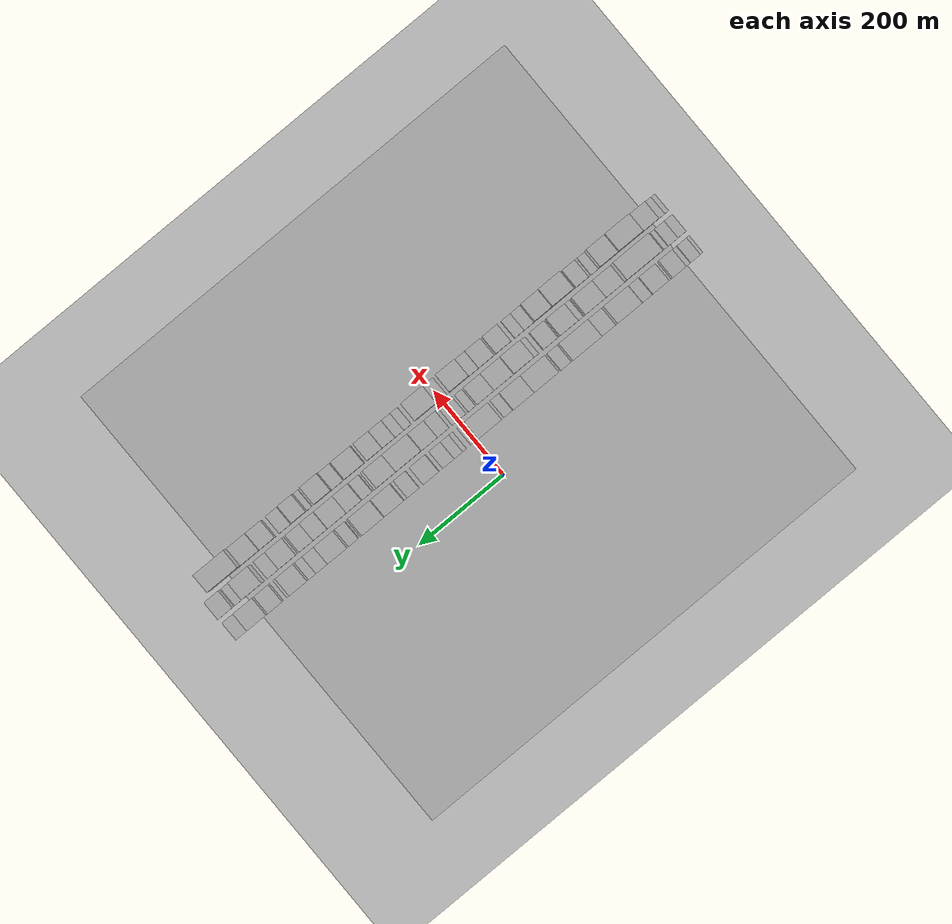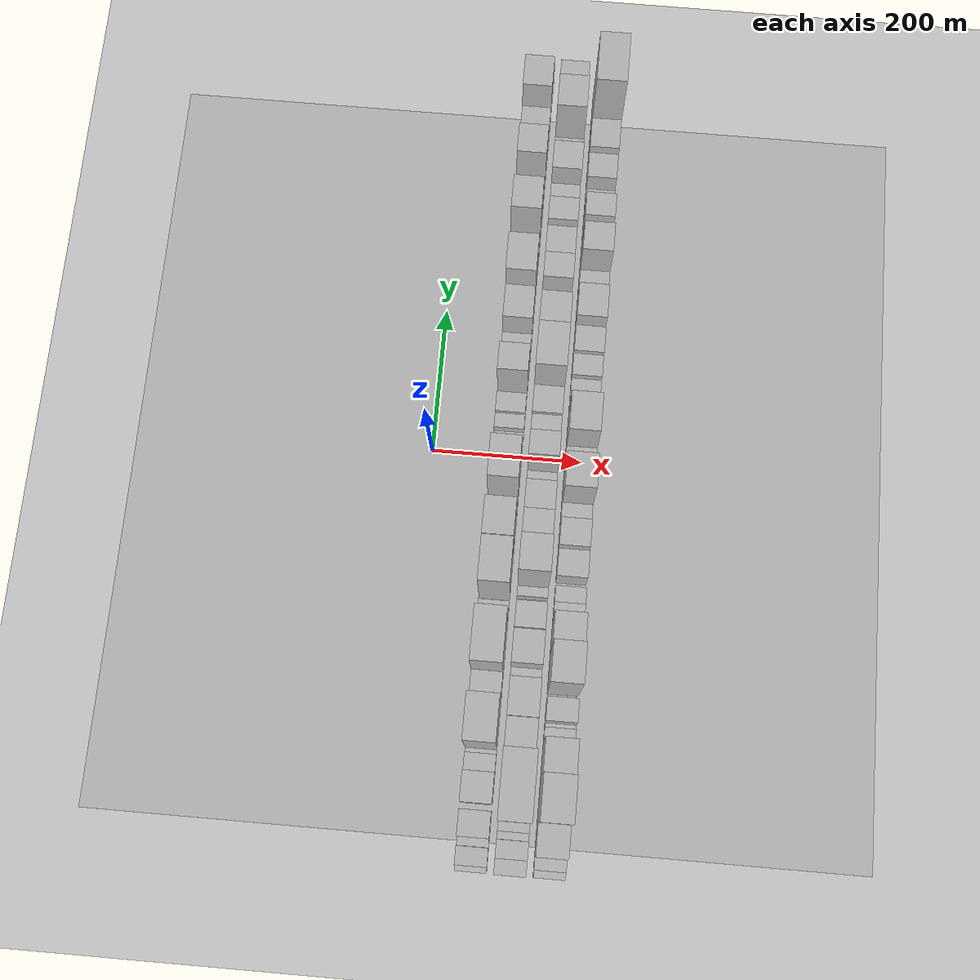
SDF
<?xml version="1.0" encoding="utf-8"?>

<sdf version="1.6">

   <world name="default">

      <gui fullscreen="0">

         <camera name="user_camera">

            <pose>-15 0 4.57585 0 0 0</pose>

            <view_controller>orbit</view_controller>

         </camera>

      </gui>

      <scene>

         <sky>

           <clouds>

             <speed>12</speed>

           </clouds>

         </sky>

         <ambient>0.4 0.4 0.4 1</ambient>

         <background>0.7 0.7 0.7 1</background>

         <shadows>1</shadows>

      </scene>

      <gravity>0 0 -9.8066</gravity>

      <magnetic_field>6e-06 2.3e-05 -4.2e-05</magnetic_field>

      <physics default="0" name="default_physics" type="ode">

         <ode>

            <solver>

               <type>quick</type>

               <iters>10</iters>

               <sor>1.0</sor>

               <use_dynamic_moi_rescaling>0</use_dynamic_moi_rescaling>

            </solver>

            <constraints>

               <cfm>0</cfm>

               <erp>0.2</erp>

               <contact_max_correcting_vel>100</contact_max_correcting_vel>

               <contact_surface_layer>0.001</contact_surface_layer>

            </constraints>

         </ode>

         <max_step_size>0.004</max_step_size>

         <real_time_factor>1</real_time_factor>

         <real_time_update_rate>250</real_time_update_rate>

      </physics>

      <light name="sun" type="directional">

         <cast_shadows>1</cast_shadows>

         <pose>0 0 10 0 0 0</pose>

         <diffuse>0.8 0.8 0.8 1</diffuse>

         <specular>0.2 0.2 0.2 1</specular>

         <attenuation>

            <range>1000</range>

            <constant>0.9</constant>

            <linear>0.01</linear>

            <quadratic>0.001</quadratic>

         </attenuation>

         <direction>-0.5 0.1 -0.9</direction>

      </light>

      <include>

         <name>ground_plane_1</name>

         <uri>model://HANNAS_ground_plane</uri>

         <pose>0 0 0  0 0 0</pose>

      </include>

      <include>

         <name>ground_plane_2</name>

         <uri>model://HANNAS_ground_plane</uri>

         <pose>100 0 0  0 0 0</pose>

      </include>

      <model name="building_1">

         <static>1</static>

         <pose frame="">100.0000 -532.1938 0 0.000000 0.000000 0.000000</pose>

         <link name="link">

            <pose frame="">0 0 9.00 0 0 0</pose>

            <collision name="collision">

               <geometry>

                  <box>

                     <size>40.0000 7.6124 18.0000</size>

                  </box>

               </geometry>

               <max_contacts>10</max_contacts>

               <surface>

                  <contact>

                     <ode/>

                  </contact>

                  <bounce/>

                  <friction>

                     <torsional>

                        <ode/>

                     </torsional>

                     <ode/>

                  </friction>

               </surface>

            </collision>

            <visual name="visual">

               <cast_shadows>0</cast_shadows>

               <geometry>

                  <box>

                     <size>40.0000 7.6124 18.0000</size>

                  </box>

               </geometry>

               <material>

                  <script>

                     <uri>model://HANNAS_wall/materials/scripts</uri>

                     <uri>model://HANNAS_wall/materials/textures</uri>

                     <name>vrc/HANNAS_wall</name>

                  </script>

               </material>

            </visual>

            <self_collide>0</self_collide>

            <enable_wind>0</enable_wind>

            <kinematic>0</kinematic>

         </link>

      </model>

      <model name="building_2">

         <static>1</static>

         <pose frame="">100.0000 -516.9038 0 0.000000 0.000000 0.000000</pose>

         <link name="link">

            <pose frame="">0 0 21.00 0 0 0</pose>

            <collision name="collision">

               <geometry>

                  <box>

                     <size>40.0000 22.9676 42.0000</size>

                  </box>

               </geometry>

               <max_contacts>10</max_contacts>

               <surface>

                  <contact>

                     <ode/>

                  </contact>

                  <bounce/>

                  <friction>

                     <torsional>

                        <ode/>

                     </torsional>

                     <ode/>

                  </friction>

               </surface>

            </collision>

            <visual name="visual">

               <cast_shadows>0</cast_shadows>

               <geometry>

                  <box>

                     <size>40.0000 22.9676 42.0000</size>

                  </box>

               </geometry>

               <material>

                  <script>

                     <uri>model://HANNAS_wall/materials/scripts</uri>

                     <uri>model://HANNAS_wall/materials/textures</uri>

                     <name>vrc/HANNAS_wall</name>

                  </script>

               </material>

            </visual>

            <self_collide>0</self_collide>

            <enable_wind>0</enable_wind>

            <kinematic>0</kinematic>

         </link>

      </model>

      <model name="building_3">

         <static>1</static>

         <pose frame="">100.0000 -499.8165 0 0.000000 0.000000 0.000000</pose>

         <link name="link">

            <pose frame="">0 0 12.00 0 0 0</pose>

            <collision name="collision">

               <geometry>

                  <box>

                     <size>40.0000 11.2069 24.0000</size>

                  </box>

               </geometry>

               <max_contacts>10</max_contacts>

               <surface>

                  <contact>

                     <ode/>

                  </contact>

                  <bounce/>

                  <friction>

                     <torsional>

                        <ode/>

                     </torsional>

                     <ode/>

                  </friction>

               </surface>

            </collision>

            <visual name="visual">

               <cast_shadows>0</cast_shadows>

               <geometry>

                  <box>

                     <size>40.0000 11.2069 24.0000</size>

                  </box>

               </geometry>

               <material>

                  <script>

                     <uri>model://HANNAS_wall/materials/scripts</uri>

                     <uri>model://HANNAS_wall/materials/textures</uri>

                     <name>vrc/HANNAS_wall</name>

                  </script>

               </material>

            </visual>

            <self_collide>0</self_collide>

            <enable_wind>0</enable_wind>

            <kinematic>0</kinematic>

         </link>

      </model>

      <model name="building_4">

         <static>1</static>

         <pose frame="">100.0000 -477.8729 0 0.000000 0.000000 0.000000</pose>

         <link name="link">

            <pose frame="">0 0 30.00 0 0 0</pose>

            <collision name="collision">

               <geometry>

                  <box>

                     <size>40.0000 32.6803 60.0000</size>

                  </box>

               </geometry>

               <max_contacts>10</max_contacts>

               <surface>

                  <contact>

                     <ode/>

                  </contact>

                  <bounce/>

                  <friction>

                     <torsional>

                        <ode/>

                     </torsional>

                     <ode/>

                  </friction>

               </surface>

            </collision>

            <visual name="visual">

               <cast_shadows>0</cast_shadows>

               <geometry>

                  <box>

                     <size>40.0000 32.6803 60.0000</size>

                  </box>

               </geometry>

               <material>

                  <script>

                     <uri>model://HANNAS_wall/materials/scripts</uri>

                     <uri>model://HANNAS_wall/materials/textures</uri>

                     <name>vrc/HANNAS_wall</name>

                  </script>

               </material>

            </visual>

            <self_collide>0</self_collide>

            <enable_wind>0</enable_wind>

            <kinematic>0</kinematic>

         </link>

      </model>

      <model name="building_5">

         <static>1</static>

         <pose frame="">100.0000 -434.3912 0 0.000000 0.000000 0.000000</pose>

         <link name="link">

            <pose frame="">0 0 34.50 0 0 0</pose>

            <collision name="collision">

               <geometry>

                  <box>

                     <size>40.0000 38.2831 69.0000</size>

                  </box>

               </geometry>

               <max_contacts>10</max_contacts>

               <surface>

                  <contact>

                     <ode/>

                  </contact>

                  <bounce/>

                  <friction>

                     <torsional>

                        <ode/>

                     </torsional>

                     <ode/>

                  </friction>

               </surface>

            </collision>

            <visual name="visual">

               <cast_shadows>0</cast_shadows>

               <geometry>

                  <box>

                     <size>40.0000 38.2831 69.0000</size>

                  </box>

               </geometry>

               <material>

                  <script>

                     <uri>model://HANNAS_wall/materials/scripts</uri>

                     <uri>model://HANNAS_wall/materials/textures</uri>

                     <name>vrc/HANNAS_wall</name>

                  </script>

               </material>

            </visual>

            <self_collide>0</self_collide>

            <enable_wind>0</enable_wind>

            <kinematic>0</kinematic>

         </link>

      </model>

      <model name="building_6">

         <static>1</static>

         <pose frame="">100.0000 -403.8500 0 0.000000 0.000000 0.000000</pose>

         <link name="link">

            <pose frame="">0 0 19.50 0 0 0</pose>

            <collision name="collision">

               <geometry>

                  <box>

                     <size>40.0000 22.7993 39.0000</size>

                  </box>

               </geometry>

               <max_contacts>10</max_contacts>

               <surface>

                  <contact>

                     <ode/>

                  </contact>

                  <bounce/>

                  <friction>

                     <torsional>

                        <ode/>

                     </torsional>

                     <ode/>

                  </friction>

               </surface>

            </collision>

            <visual name="visual">

               <cast_shadows>0</cast_shadows>

               <geometry>

                  <box>

                     <size>40.0000 22.7993 39.0000</size>

                  </box>

               </geometry>

               <material>

                  <script>

                     <uri>model://HANNAS_wall/materials/scripts</uri>

                     <uri>model://HANNAS_wall/materials/textures</uri>

                     <name>vrc/HANNAS_wall</name>

                  </script>

               </material>

            </visual>

            <self_collide>0</self_collide>

            <enable_wind>0</enable_wind>

            <kinematic>0</kinematic>

         </link>

      </model>

      <model name="building_7">

         <static>1</static>

         <pose frame="">100.0000 -389.1463 0 0.000000 0.000000 0.000000</pose>

         <link name="link">

            <pose frame="">0 0 7.50 0 0 0</pose>

            <collision name="collision">

               <geometry>

                  <box>

                     <size>40.0000 6.6081 15.0000</size>

                  </box>

               </geometry>

               <max_contacts>10</max_contacts>

               <surface>

                  <contact>

                     <ode/>

                  </contact>

                  <bounce/>

                  <friction>

                     <torsional>

                        <ode/>

                     </torsional>

                     <ode/>

                  </friction>

               </surface>

            </collision>

            <visual name="visual">

               <cast_shadows>0</cast_shadows>

               <geometry>

                  <box>

                     <size>40.0000 6.6081 15.0000</size>

                  </box>

               </geometry>

               <material>

                  <script>

                     <uri>model://HANNAS_wall/materials/scripts</uri>

                     <uri>model://HANNAS_wall/materials/textures</uri>

                     <name>vrc/HANNAS_wall</name>

                  </script>

               </material>

            </visual>

            <self_collide>0</self_collide>

            <enable_wind>0</enable_wind>

            <kinematic>0</kinematic>

         </link>

      </model>

      <model name="building_8">

         <static>1</static>

         <pose frame="">100.0000 -357.1126 0 0.000000 0.000000 0.000000</pose>

         <link name="link">

            <pose frame="">0 0 87.00 0 0 0</pose>

            <collision name="collision">

               <geometry>

                  <box>

                     <size>40.0000 57.4594 174.0000</size>

                  </box>

               </geometry>

               <max_contacts>10</max_contacts>

               <surface>

                  <contact>

                     <ode/>

                  </contact>

                  <bounce/>

                  <friction>

                     <torsional>

                        <ode/>

                     </torsional>

                     <ode/>

                  </friction>

               </surface>

            </collision>

            <visual name="visual">

               <cast_shadows>0</cast_shadows>

               <geometry>

                  <box>

                     <size>40.0000 57.4594 174.0000</size>

                  </box>

               </geometry>

               <material>

                  <script>

                     <uri>model://HANNAS_wall/materials/scripts</uri>

                     <uri>model://HANNAS_wall/materials/textures</uri>

                     <name>vrc/HANNAS_wall</name>

                  </script>

               </material>

            </visual>

            <self_collide>0</self_collide>

            <enable_wind>0</enable_wind>

            <kinematic>0</kinematic>

         </link>

      </model>

      <model name="building_9">

         <static>1</static>

         <pose frame="">100.0000 -310.5954 0 0.000000 0.000000 0.000000</pose>

         <link name="link">

            <pose frame="">0 0 34.50 0 0 0</pose>

            <collision name="collision">

               <geometry>

                  <box>

                     <size>40.0000 35.5749 69.0000</size>

                  </box>

               </geometry>

               <max_contacts>10</max_contacts>

               <surface>

                  <contact>

                     <ode/>

                  </contact>

                  <bounce/>

                  <friction>

                     <torsional>

                        <ode/>

                     </torsional>

                     <ode/>

                  </friction>

               </surface>

            </collision>

            <visual name="visual">

               <cast_shadows>0</cast_shadows>

               <geometry>

                  <box>

                     <size>40.0000 35.5749 69.0000</size>

                  </box>

               </geometry>

               <material>

                  <script>

                     <uri>model://HANNAS_wall/materials/scripts</uri>

                     <uri>model://HANNAS_wall/materials/textures</uri>

                     <name>vrc/HANNAS_wall</name>

                  </script>

               </material>

            </visual>

            <self_collide>0</self_collide>

            <enable_wind>0</enable_wind>

            <kinematic>0</kinematic>

         </link>

      </model>

      <model name="building_10">

         <static>1</static>

         <pose frame="">100.0000 -258.9079 0 0.000000 0.000000 0.000000</pose>

         <link name="link">

            <pose frame="">0 0 85.50 0 0 0</pose>

            <collision name="collision">

               <geometry>

                  <box>

                     <size>40.0000 67.8001 171.0000</size>

                  </box>

               </geometry>

               <max_contacts>10</max_contacts>

               <surface>

                  <contact>

                     <ode/>

                  </contact>

                  <bounce/>

                  <friction>

                     <torsional>

                        <ode/>

                     </torsional>

                     <ode/>

                  </friction>

               </surface>

            </collision>

            <visual name="visual">

               <cast_shadows>0</cast_shadows>

               <geometry>

                  <box>

                     <size>40.0000 67.8001 171.0000</size>

                  </box>

               </geometry>

               <material>

                  <script>

                     <uri>model://HANNAS_wall/materials/scripts</uri>

                     <uri>model://HANNAS_wall/materials/textures</uri>

                     <name>vrc/HANNAS_wall</name>

                  </script>

               </material>

            </visual>

            <self_collide>0</self_collide>

            <enable_wind>0</enable_wind>

            <kinematic>0</kinematic>

         </link>

      </model>

      <model name="building_11">

         <static>1</static>

         <pose frame="">100.0000 -212.6583 0 0.000000 0.000000 0.000000</pose>

         <link name="link">

            <pose frame="">0 0 22.50 0 0 0</pose>

            <collision name="collision">

               <geometry>

                  <box>

                     <size>40.0000 24.6991 45.0000</size>

                  </box>

               </geometry>

               <max_contacts>10</max_contacts>

               <surface>

                  <contact>

                     <ode/>

                  </contact>

                  <bounce/>

                  <friction>

                     <torsional>

                        <ode/>

                     </torsional>

                     <ode/>

                  </friction>

               </surface>

            </collision>

            <visual name="visual">

               <cast_shadows>0</cast_shadows>

               <geometry>

                  <box>

                     <size>40.0000 24.6991 45.0000</size>

                  </box>

               </geometry>

               <material>

                  <script>

                     <uri>model://HANNAS_wall/materials/scripts</uri>

                     <uri>model://HANNAS_wall/materials/textures</uri>

                     <name>vrc/HANNAS_wall</name>

                  </script>

               </material>

            </visual>

            <self_collide>0</self_collide>

            <enable_wind>0</enable_wind>

            <kinematic>0</kinematic>

         </link>

      </model>

      <model name="building_12">

         <static>1</static>

         <pose frame="">100.0000 -164.6180 0 0.000000 0.000000 0.000000</pose>

         <link name="link">

            <pose frame="">0 0 73.50 0 0 0</pose>

            <collision name="collision">

               <geometry>

                  <box>

                     <size>40.0000 57.3815 147.0000</size>

                  </box>

               </geometry>

               <max_contacts>10</max_contacts>

               <surface>

                  <contact>

                     <ode/>

                  </contact>

                  <bounce/>

                  <friction>

                     <torsional>

                        <ode/>

                     </torsional>

                     <ode/>

                  </friction>

               </surface>

            </collision>

            <visual name="visual">

               <cast_shadows>0</cast_shadows>

               <geometry>

                  <box>

                     <size>40.0000 57.3815 147.0000</size>

                  </box>

               </geometry>

               <material>

                  <script>

                     <uri>model://HANNAS_wall/materials/scripts</uri>

                     <uri>model://HANNAS_wall/materials/textures</uri>

                     <name>vrc/HANNAS_wall</name>

                  </script>

               </material>

            </visual>

            <self_collide>0</self_collide>

            <enable_wind>0</enable_wind>

            <kinematic>0</kinematic>

         </link>

      </model>

      <model name="building_13">

         <static>1</static>

         <pose frame="">100.0000 -111.6563 0 0.000000 0.000000 0.000000</pose>

         <link name="link">

            <pose frame="">0 0 75.00 0 0 0</pose>

            <collision name="collision">

               <geometry>

                  <box>

                     <size>40.0000 48.5418 150.0000</size>

                  </box>

               </geometry>

               <max_contacts>10</max_contacts>

               <surface>

                  <contact>

                     <ode/>

                  </contact>

                  <bounce/>

                  <friction>

                     <torsional>

                        <ode/>

                     </torsional>

                     <ode/>

                  </friction>

               </surface>

            </collision>

            <visual name="visual">

               <cast_shadows>0</cast_shadows>

               <geometry>

                  <box>

                     <size>40.0000 48.5418 150.0000</size>

                  </box>

               </geometry>

               <material>

                  <script>

                     <uri>model://HANNAS_wall/materials/scripts</uri>

                     <uri>model://HANNAS_wall/materials/textures</uri>

                     <name>vrc/HANNAS_wall</name>

                  </script>

               </material>

            </visual>

            <self_collide>0</self_collide>

            <enable_wind>0</enable_wind>

            <kinematic>0</kinematic>

         </link>

      </model>

      <model name="building_14">

         <static>1</static>

         <pose frame="">100.0000 -77.1205 0 0.000000 0.000000 0.000000</pose>

         <link name="link">

            <pose frame="">0 0 18.00 0 0 0</pose>

            <collision name="collision">

               <geometry>

                  <box>

                     <size>40.0000 20.5298 36.0000</size>

                  </box>

               </geometry>

               <max_contacts>10</max_contacts>

               <surface>

                  <contact>

                     <ode/>

                  </contact>

                  <bounce/>

                  <friction>

                     <torsional>

                        <ode/>

                     </torsional>

                     <ode/>

                  </friction>

               </surface>

            </collision>

            <visual name="visual">

               <cast_shadows>0</cast_shadows>

               <geometry>

                  <box>

                     <size>40.0000 20.5298 36.0000</size>

                  </box>

               </geometry>

               <material>

                  <script>

                     <uri>model://HANNAS_wall/materials/scripts</uri>

                     <uri>model://HANNAS_wall/materials/textures</uri>

                     <name>vrc/HANNAS_wall</name>

                  </script>

               </material>

            </visual>

            <self_collide>0</self_collide>

            <enable_wind>0</enable_wind>

            <kinematic>0</kinematic>

         </link>

      </model>

      <model name="building_15">

         <static>1</static>

         <pose frame="">100.0000 -33.4016 0 0.000000 0.000000 0.000000</pose>

         <link name="link">

            <pose frame="">0 0 70.50 0 0 0</pose>

            <collision name="collision">

               <geometry>

                  <box>

                     <size>40.0000 54.9079 141.0000</size>

                  </box>

               </geometry>

               <max_contacts>10</max_contacts>

               <surface>

                  <contact>

                     <ode/>

                  </contact>

                  <bounce/>

                  <friction>

                     <torsional>

                        <ode/>

                     </torsional>

                     <ode/>

                  </friction>

               </surface>

            </collision>

            <visual name="visual">

               <cast_shadows>0</cast_shadows>

               <geometry>

                  <box>

                     <size>40.0000 54.9079 141.0000</size>

                  </box>

               </geometry>

               <material>

                  <script>

                     <uri>model://HANNAS_wall/materials/scripts</uri>

                     <uri>model://HANNAS_wall/materials/textures</uri>

                     <name>vrc/HANNAS_wall</name>

                  </script>

               </material>

            </visual>

            <self_collide>0</self_collide>

            <enable_wind>0</enable_wind>

            <kinematic>0</kinematic>

         </link>

      </model>

      <model name="building_16">

         <static>1</static>

         <pose frame="">100.0000 5.5530 0 0.000000 0.000000 0.000000</pose>

         <link name="link">

            <pose frame="">0 0 12.00 0 0 0</pose>

            <collision name="collision">

               <geometry>

                  <box>

                     <size>40.0000 11.0014 24.0000</size>

                  </box>

               </geometry>

               <max_contacts>10</max_contacts>

               <surface>

                  <contact>

                     <ode/>

                  </contact>

                  <bounce/>

                  <friction>

                     <torsional>

                        <ode/>

                     </torsional>

                     <ode/>

                  </friction>

               </surface>

            </collision>

            <visual name="visual">

               <cast_shadows>0</cast_shadows>

               <geometry>

                  <box>

                     <size>40.0000 11.0014 24.0000</size>

                  </box>

               </geometry>

               <material>

                  <script>

                     <uri>model://HANNAS_wall/materials/scripts</uri>

                     <uri>model://HANNAS_wall/materials/textures</uri>

                     <name>vrc/HANNAS_wall</name>

                  </script>

               </material>

            </visual>

            <self_collide>0</self_collide>

            <enable_wind>0</enable_wind>

            <kinematic>0</kinematic>

         </link>

      </model>

      <model name="building_17">

         <static>1</static>

         <pose frame="">100.0000 25.5360 0 0.000000 0.000000 0.000000</pose>

         <link name="link">

            <pose frame="">0 0 10.50 0 0 0</pose>

            <collision name="collision">

               <geometry>

                  <box>

                     <size>40.0000 8.9645 21.0000</size>

                  </box>

               </geometry>

               <max_contacts>10</max_contacts>

               <surface>

                  <contact>

                     <ode/>

                  </contact>

                  <bounce/>

                  <friction>

                     <torsional>

                        <ode/>

                     </torsional>

                     <ode/>

                  </friction>

               </surface>

            </collision>

            <visual name="visual">

               <cast_shadows>0</cast_shadows>

               <geometry>

                  <box>

                     <size>40.0000 8.9645 21.0000</size>

                  </box>

               </geometry>

               <material>

                  <script>

                     <uri>model://HANNAS_wall/materials/scripts</uri>

                     <uri>model://HANNAS_wall/materials/textures</uri>

                     <name>vrc/HANNAS_wall</name>

                  </script>

               </material>

            </visual>

            <self_collide>0</self_collide>

            <enable_wind>0</enable_wind>

            <kinematic>0</kinematic>

         </link>

      </model>

      <model name="building_18">

         <static>1</static>

         <pose frame="">100.0000 39.9722 0 0.000000 0.000000 0.000000</pose>

         <link name="link">

            <pose frame="">0 0 19.50 0 0 0</pose>

            <collision name="collision">

               <geometry>

                  <box>

                     <size>40.0000 19.9079 39.0000</size>

                  </box>

               </geometry>

               <max_contacts>10</max_contacts>

               <surface>

                  <contact>

                     <ode/>

                  </contact>

                  <bounce/>

                  <friction>

                     <torsional>

                        <ode/>

                     </torsional>

                     <ode/>

                  </friction>

               </surface>

            </collision>

            <visual name="visual">

               <cast_shadows>0</cast_shadows>

               <geometry>

                  <box>

                     <size>40.0000 19.9079 39.0000</size>

                  </box>

               </geometry>

               <material>

                  <script>

                     <uri>model://HANNAS_wall/materials/scripts</uri>

                     <uri>model://HANNAS_wall/materials/textures</uri>

                     <name>vrc/HANNAS_wall</name>

                  </script>

               </material>

            </visual>

            <self_collide>0</self_collide>

            <enable_wind>0</enable_wind>

            <kinematic>0</kinematic>

         </link>

      </model>

      <model name="building_19">

         <static>1</static>

         <pose frame="">100.0000 63.5394 0 0.000000 0.000000 0.000000</pose>

         <link name="link">

            <pose frame="">0 0 24.00 0 0 0</pose>

            <collision name="collision">

               <geometry>

                  <box>

                     <size>40.0000 27.2266 48.0000</size>

                  </box>

               </geometry>

               <max_contacts>10</max_contacts>

               <surface>

                  <contact>

                     <ode/>

                  </contact>

                  <bounce/>

                  <friction>

                     <torsional>

                        <ode/>

                     </torsional>

                     <ode/>

                  </friction>

               </surface>

            </collision>

            <visual name="visual">

               <cast_shadows>0</cast_shadows>

               <geometry>

                  <box>

                     <size>40.0000 27.2266 48.0000</size>

                  </box>

               </geometry>

               <material>

                  <script>

                     <uri>model://HANNAS_wall/materials/scripts</uri>

                     <uri>model://HANNAS_wall/materials/textures</uri>

                     <name>vrc/HANNAS_wall</name>

                  </script>

               </material>

            </visual>

            <self_collide>0</self_collide>

            <enable_wind>0</enable_wind>

            <kinematic>0</kinematic>

         </link>

      </model>

      <model name="building_20">

         <static>1</static>

         <pose frame="">100.0000 103.5589 0 0.000000 0.000000 0.000000</pose>

         <link name="link">

            <pose frame="">0 0 60.00 0 0 0</pose>

            <collision name="collision">

               <geometry>

                  <box>

                     <size>40.0000 36.8124 120.0000</size>

                  </box>

               </geometry>

               <max_contacts>10</max_contacts>

               <surface>

                  <contact>

                     <ode/>

                  </contact>

                  <bounce/>

                  <friction>

                     <torsional>

                        <ode/>

                     </torsional>

                     <ode/>

                  </friction>

               </surface>

            </collision>

            <visual name="visual">

               <cast_shadows>0</cast_shadows>

               <geometry>

                  <box>

                     <size>40.0000 36.8124 120.0000</size>

                  </box>

               </geometry>

               <material>

                  <script>

                     <uri>model://HANNAS_wall/materials/scripts</uri>

                     <uri>model://HANNAS_wall/materials/textures</uri>

                     <name>vrc/HANNAS_wall</name>

                  </script>

               </material>

            </visual>

            <self_collide>0</self_collide>

            <enable_wind>0</enable_wind>

            <kinematic>0</kinematic>

         </link>

      </model>

      <model name="building_21">

         <static>1</static>

         <pose frame="">100.0000 146.1554 0 0.000000 0.000000 0.000000</pose>

         <link name="link">

            <pose frame="">0 0 24.00 0 0 0</pose>

            <collision name="collision">

               <geometry>

                  <box>

                     <size>40.0000 28.3807 48.0000</size>

                  </box>

               </geometry>

               <max_contacts>10</max_contacts>

               <surface>

                  <contact>

                     <ode/>

                  </contact>

                  <bounce/>

                  <friction>

                     <torsional>

                        <ode/>

                     </torsional>

                     <ode/>

                  </friction>

               </surface>

            </collision>

            <visual name="visual">

               <cast_shadows>0</cast_shadows>

               <geometry>

                  <box>

                     <size>40.0000 28.3807 48.0000</size>

                  </box>

               </geometry>

               <material>

                  <script>

                     <uri>model://HANNAS_wall/materials/scripts</uri>

                     <uri>model://HANNAS_wall/materials/textures</uri>

                     <name>vrc/HANNAS_wall</name>

                  </script>

               </material>

            </visual>

            <self_collide>0</self_collide>

            <enable_wind>0</enable_wind>

            <kinematic>0</kinematic>

         </link>

      </model>

      <model name="building_22">

         <static>1</static>

         <pose frame="">100.0000 163.9372 0 0.000000 0.000000 0.000000</pose>

         <link name="link">

            <pose frame="">0 0 7.50 0 0 0</pose>

            <collision name="collision">

               <geometry>

                  <box>

                     <size>40.0000 7.1829 15.0000</size>

                  </box>

               </geometry>

               <max_contacts>10</max_contacts>

               <surface>

                  <contact>

                     <ode/>

                  </contact>

                  <bounce/>

                  <friction>

                     <torsional>

                        <ode/>

                     </torsional>

                     <ode/>

                  </friction>

               </surface>

            </collision>

            <visual name="visual">

               <cast_shadows>0</cast_shadows>

               <geometry>

                  <box>

                     <size>40.0000 7.1829 15.0000</size>

                  </box>

               </geometry>

               <material>

                  <script>

                     <uri>model://HANNAS_wall/materials/scripts</uri>

                     <uri>model://HANNAS_wall/materials/textures</uri>

                     <name>vrc/HANNAS_wall</name>

                  </script>

               </material>

            </visual>

            <self_collide>0</self_collide>

            <enable_wind>0</enable_wind>

            <kinematic>0</kinematic>

         </link>

      </model>

      <model name="building_23">

         <static>1</static>

         <pose frame="">100.0000 190.2346 0 0.000000 0.000000 0.000000</pose>

         <link name="link">

            <pose frame="">0 0 45.00 0 0 0</pose>

            <collision name="collision">

               <geometry>

                  <box>

                     <size>40.0000 45.4119 90.0000</size>

                  </box>

               </geometry>

               <max_contacts>10</max_contacts>

               <surface>

                  <contact>

                     <ode/>

                  </contact>

                  <bounce/>

                  <friction>

                     <torsional>

                        <ode/>

                     </torsional>

                     <ode/>

                  </friction>

               </surface>

            </collision>

            <visual name="visual">

               <cast_shadows>0</cast_shadows>

               <geometry>

                  <box>

                     <size>40.0000 45.4119 90.0000</size>

                  </box>

               </geometry>

               <material>

                  <script>

                     <uri>model://HANNAS_wall/materials/scripts</uri>

                     <uri>model://HANNAS_wall/materials/textures</uri>

                     <name>vrc/HANNAS_wall</name>

                  </script>

               </material>

            </visual>

            <self_collide>0</self_collide>

            <enable_wind>0</enable_wind>

            <kinematic>0</kinematic>

         </link>

      </model>

      <model name="building_24">

         <static>1</static>

         <pose frame="">100.0000 238.6542 0 0.000000 0.000000 0.000000</pose>

         <link name="link">

            <pose frame="">0 0 72.00 0 0 0</pose>

            <collision name="collision">

               <geometry>

                  <box>

                     <size>40.0000 51.4272 144.0000</size>

                  </box>

               </geometry>

               <max_contacts>10</max_contacts>

               <surface>

                  <contact>

                     <ode/>

                  </contact>

                  <bounce/>

                  <friction>

                     <torsional>

                        <ode/>

                     </torsional>

                     <ode/>

                  </friction>

               </surface>

            </collision>

            <visual name="visual">

               <cast_shadows>0</cast_shadows>

               <geometry>

                  <box>

                     <size>40.0000 51.4272 144.0000</size>

                  </box>

               </geometry>

               <material>

                  <script>

                     <uri>model://HANNAS_wall/materials/scripts</uri>

                     <uri>model://HANNAS_wall/materials/textures</uri>

                     <name>vrc/HANNAS_wall</name>

                  </script>

               </material>

            </visual>

            <self_collide>0</self_collide>

            <enable_wind>0</enable_wind>

            <kinematic>0</kinematic>

         </link>

      </model>

      <model name="building_25">

         <static>1</static>

         <pose frame="">100.0000 267.7505 0 0.000000 0.000000 0.000000</pose>

         <link name="link">

            <pose frame="">0 0 7.50 0 0 0</pose>

            <collision name="collision">

               <geometry>

                  <box>

                     <size>40.0000 6.7653 15.0000</size>

                  </box>

               </geometry>

               <max_contacts>10</max_contacts>

               <surface>

                  <contact>

                     <ode/>

                  </contact>

                  <bounce/>

                  <friction>

                     <torsional>

                        <ode/>

                     </torsional>

                     <ode/>

                  </friction>

               </surface>

            </collision>

            <visual name="visual">

               <cast_shadows>0</cast_shadows>

               <geometry>

                  <box>

                     <size>40.0000 6.7653 15.0000</size>

                  </box>

               </geometry>

               <material>

                  <script>

                     <uri>model://HANNAS_wall/materials/scripts</uri>

                     <uri>model://HANNAS_wall/materials/textures</uri>

                     <name>vrc/HANNAS_wall</name>

                  </script>

               </material>

            </visual>

            <self_collide>0</self_collide>

            <enable_wind>0</enable_wind>

            <kinematic>0</kinematic>

         </link>

      </model>

      <model name="building_26">

         <static>1</static>

         <pose frame="">100.0000 286.7399 0 0.000000 0.000000 0.000000</pose>

         <link name="link">

            <pose frame="">0 0 21.00 0 0 0</pose>

            <collision name="collision">

               <geometry>

                  <box>

                     <size>40.0000 23.2135 42.0000</size>

                  </box>

               </geometry>

               <max_contacts>10</max_contacts>

               <surface>

                  <contact>

                     <ode/>

                  </contact>

                  <bounce/>

                  <friction>

                     <torsional>

                        <ode/>

                     </torsional>

                     <ode/>

                  </friction>

               </surface>

            </collision>

            <visual name="visual">

               <cast_shadows>0</cast_shadows>

               <geometry>

                  <box>

                     <size>40.0000 23.2135 42.0000</size>

                  </box>

               </geometry>

               <material>

                  <script>

                     <uri>model://HANNAS_wall/materials/scripts</uri>

                     <uri>model://HANNAS_wall/materials/textures</uri>

                     <name>vrc/HANNAS_wall</name>

                  </script>

               </material>

            </visual>

            <self_collide>0</self_collide>

            <enable_wind>0</enable_wind>

            <kinematic>0</kinematic>

         </link>

      </model>

      <model name="building_27">

         <static>1</static>

         <pose frame="">100.0000 320.9739 0 0.000000 0.000000 0.000000</pose>

         <link name="link">

            <pose frame="">0 0 73.50 0 0 0</pose>

            <collision name="collision">

               <geometry>

                  <box>

                     <size>40.0000 45.2546 147.0000</size>

                  </box>

               </geometry>

               <max_contacts>10</max_contacts>

               <surface>

                  <contact>

                     <ode/>

                  </contact>

                  <bounce/>

                  <friction>

                     <torsional>

                        <ode/>

                     </torsional>

                     <ode/>

                  </friction>

               </surface>

            </collision>

            <visual name="visual">

               <cast_shadows>0</cast_shadows>

               <geometry>

                  <box>

                     <size>40.0000 45.2546 147.0000</size>

                  </box>

               </geometry>

               <material>

                  <script>

                     <uri>model://HANNAS_wall/materials/scripts</uri>

                     <uri>model://HANNAS_wall/materials/textures</uri>

                     <name>vrc/HANNAS_wall</name>

                  </script>

               </material>

            </visual>

            <self_collide>0</self_collide>

            <enable_wind>0</enable_wind>

            <kinematic>0</kinematic>

         </link>

      </model>

      <model name="building_28">

         <static>1</static>

         <pose frame="">100.0000 358.9560 0 0.000000 0.000000 0.000000</pose>

         <link name="link">

            <pose frame="">0 0 27.00 0 0 0</pose>

            <collision name="collision">

               <geometry>

                  <box>

                     <size>40.0000 30.7095 54.0000</size>

                  </box>

               </geometry>

               <max_contacts>10</max_contacts>

               <surface>

                  <contact>

                     <ode/>

                  </contact>

                  <bounce/>

                  <friction>

                     <torsional>

                        <ode/>

                     </torsional>

                     <ode/>

                  </friction>

               </surface>

            </collision>

            <visual name="visual">

               <cast_shadows>0</cast_shadows>

               <geometry>

                  <box>

                     <size>40.0000 30.7095 54.0000</size>

                  </box>

               </geometry>

               <material>

                  <script>

                     <uri>model://HANNAS_wall/materials/scripts</uri>

                     <uri>model://HANNAS_wall/materials/textures</uri>

                     <name>vrc/HANNAS_wall</name>

                  </script>

               </material>

            </visual>

            <self_collide>0</self_collide>

            <enable_wind>0</enable_wind>

            <kinematic>0</kinematic>

         </link>

      </model>

      <model name="building_29">

         <static>1</static>

         <pose frame="">100.0000 383.4012 0 0.000000 0.000000 0.000000</pose>

         <link name="link">

            <pose frame="">0 0 18.00 0 0 0</pose>

            <collision name="collision">

               <geometry>

                  <box>

                     <size>40.0000 18.1811 36.0000</size>

                  </box>

               </geometry>

               <max_contacts>10</max_contacts>

               <surface>

                  <contact>

                     <ode/>

                  </contact>

                  <bounce/>

                  <friction>

                     <torsional>

                        <ode/>

                     </torsional>

                     <ode/>

                  </friction>

               </surface>

            </collision>

            <visual name="visual">

               <cast_shadows>0</cast_shadows>

               <geometry>

                  <box>

                     <size>40.0000 18.1811 36.0000</size>

                  </box>

               </geometry>

               <material>

                  <script>

                     <uri>model://HANNAS_wall/materials/scripts</uri>

                     <uri>model://HANNAS_wall/materials/textures</uri>

                     <name>vrc/HANNAS_wall</name>

                  </script>

               </material>

            </visual>

            <self_collide>0</self_collide>

            <enable_wind>0</enable_wind>

            <kinematic>0</kinematic>

         </link>

      </model>

      <model name="building_30">

         <static>1</static>

         <pose frame="">100.0000 413.2691 0 0.000000 0.000000 0.000000</pose>

         <link name="link">

            <pose frame="">0 0 58.50 0 0 0</pose>

            <collision name="collision">

               <geometry>

                  <box>

                     <size>40.0000 41.5546 117.0000</size>

                  </box>

               </geometry>

               <max_contacts>10</max_contacts>

               <surface>

                  <contact>

                     <ode/>

                  </contact>

                  <bounce/>

                  <friction>

                     <torsional>

                        <ode/>

                     </torsional>

                     <ode/>

                  </friction>

               </surface>

            </collision>

            <visual name="visual">

               <cast_shadows>0</cast_shadows>

               <geometry>

                  <box>

                     <size>40.0000 41.5546 117.0000</size>

                  </box>

               </geometry>

               <material>

                  <script>

                     <uri>model://HANNAS_wall/materials/scripts</uri>

                     <uri>model://HANNAS_wall/materials/textures</uri>

                     <name>vrc/HANNAS_wall</name>

                  </script>

               </material>

            </visual>

            <self_collide>0</self_collide>

            <enable_wind>0</enable_wind>

            <kinematic>0</kinematic>

         </link>

      </model>

      <model name="building_31">

         <static>1</static>

         <pose frame="">100.0000 438.9469 0 0.000000 0.000000 0.000000</pose>

         <link name="link">

            <pose frame="">0 0 12.00 0 0 0</pose>

            <collision name="collision">

               <geometry>

                  <box>

                     <size>40.0000 9.8010 24.0000</size>

                  </box>

               </geometry>

               <max_contacts>10</max_contacts>

               <surface>

                  <contact>

                     <ode/>

                  </contact>

                  <bounce/>

                  <friction>

                     <torsional>

                        <ode/>

                     </torsional>

                     <ode/>

                  </friction>

               </surface>

            </collision>

            <visual name="visual">

               <cast_shadows>0</cast_shadows>

               <geometry>

                  <box>

                     <size>40.0000 9.8010 24.0000</size>

                  </box>

               </geometry>

               <material>

                  <script>

                     <uri>model://HANNAS_wall/materials/scripts</uri>

                     <uri>model://HANNAS_wall/materials/textures</uri>

                     <name>vrc/HANNAS_wall</name>

                  </script>

               </material>

            </visual>

            <self_collide>0</self_collide>

            <enable_wind>0</enable_wind>

            <kinematic>0</kinematic>

         </link>

      </model>

      <model name="building_32">

         <static>1</static>

         <pose frame="">100.0000 469.9626 0 0.000000 0.000000 0.000000</pose>

         <link name="link">

            <pose frame="">0 0 33.00 0 0 0</pose>

            <collision name="collision">

               <geometry>

                  <box>

                     <size>40.0000 34.2305 66.0000</size>

                  </box>

               </geometry>

               <max_contacts>10</max_contacts>

               <surface>

                  <contact>

                     <ode/>

                  </contact>

                  <bounce/>

                  <friction>

                     <torsional>

                        <ode/>

                     </torsional>

                     <ode/>

                  </friction>

               </surface>

            </collision>

            <visual name="visual">

               <cast_shadows>0</cast_shadows>

               <geometry>

                  <box>

                     <size>40.0000 34.2305 66.0000</size>

                  </box>

               </geometry>

               <material>

                  <script>

                     <uri>model://HANNAS_wall/materials/scripts</uri>

                     <uri>model://HANNAS_wall/materials/textures</uri>

                     <name>vrc/HANNAS_wall</name>

                  </script>

               </material>

            </visual>

            <self_collide>0</self_collide>

            <enable_wind>0</enable_wind>

            <kinematic>0</kinematic>

         </link>

      </model>

      <model name="building_33">

         <static>1</static>

         <pose frame="">100.0000 509.4696 0 0.000000 0.000000 0.000000</pose>

         <link name="link">

            <pose frame="">0 0 63.00 0 0 0</pose>

            <collision name="collision">

               <geometry>

                  <box>

                     <size>40.0000 44.7833 126.0000</size>

                  </box>

               </geometry>

               <max_contacts>10</max_contacts>

               <surface>

                  <contact>

                     <ode/>

                  </contact>

                  <bounce/>

                  <friction>

                     <torsional>

                        <ode/>

                     </torsional>

                     <ode/>

                  </friction>

               </surface>

            </collision>

            <visual name="visual">

               <cast_shadows>0</cast_shadows>

               <geometry>

                  <box>

                     <size>40.0000 44.7833 126.0000</size>

                  </box>

               </geometry>

               <material>

                  <script>

                     <uri>model://HANNAS_wall/materials/scripts</uri>

                     <uri>model://HANNAS_wall/materials/textures</uri>

                     <name>vrc/HANNAS_wall</name>

                  </script>

               </material>

            </visual>

            <self_collide>0</self_collide>

            <enable_wind>0</enable_wind>

            <kinematic>0</kinematic>

         </link>

      </model>

      <model name="building_34">

         <static>1</static>

         <pose frame="">100.0000 546.9187 0 0.000000 0.000000 0.000000</pose>

         <link name="link">

            <pose frame="">0 0 27.00 0 0 0</pose>

            <collision name="collision">

               <geometry>

                  <box>

                     <size>40.0000 30.1150 54.0000</size>

                  </box>

               </geometry>

               <max_contacts>10</max_contacts>

               <surface>

                  <contact>

                     <ode/>

                  </contact>

                  <bounce/>

                  <friction>

                     <torsional>

                        <ode/>

                     </torsional>

                     <ode/>

                  </friction>

               </surface>

            </collision>

            <visual name="visual">

               <cast_shadows>0</cast_shadows>

               <geometry>

                  <box>

                     <size>40.0000 30.1150 54.0000</size>

                  </box>

               </geometry>

               <material>

                  <script>

                     <uri>model://HANNAS_wall/materials/scripts</uri>

                     <uri>model://HANNAS_wall/materials/textures</uri>

                     <name>vrc/HANNAS_wall</name>

                  </script>

               </material>

            </visual>

            <self_collide>0</self_collide>

            <enable_wind>0</enable_wind>

            <kinematic>0</kinematic>

         </link>

      </model>

      <model name="building_35">

         <static>1</static>

         <pose frame="">149.0000 -526.2612 0 0.000000 0.000000 0.000000</pose>

         <link name="link">

            <pose frame="">0 0 18.00 0 0 0</pose>

            <collision name="collision">

               <geometry>

                  <box>

                     <size>40.0000 19.4777 36.0000</size>

                  </box>

               </geometry>

               <max_contacts>10</max_contacts>

               <surface>

                  <contact>

                     <ode/>

                  </contact>

                  <bounce/>

                  <friction>

                     <torsional>

                        <ode/>

                     </torsional>

                     <ode/>

                  </friction>

               </surface>

            </collision>

            <visual name="visual">

               <cast_shadows>0</cast_shadows>

               <geometry>

                  <box>

                     <size>40.0000 19.4777 36.0000</size>

                  </box>

               </geometry>

               <material>

                  <script>

                     <uri>model://HANNAS_wall/materials/scripts</uri>

                     <uri>model://HANNAS_wall/materials/textures</uri>

                     <name>vrc/HANNAS_wall</name>

                  </script>

               </material>

            </visual>

            <self_collide>0</self_collide>

            <enable_wind>0</enable_wind>

            <kinematic>0</kinematic>

         </link>

      </model>

      <model name="building_36">

         <static>1</static>

         <pose frame="">149.0000 -505.1789 0 0.000000 0.000000 0.000000</pose>

         <link name="link">

            <pose frame="">0 0 19.50 0 0 0</pose>

            <collision name="collision">

               <geometry>

                  <box>

                     <size>40.0000 22.6869 39.0000</size>

                  </box>

               </geometry>

               <max_contacts>10</max_contacts>

               <surface>

                  <contact>

                     <ode/>

                  </contact>

                  <bounce/>

                  <friction>

                     <torsional>

                        <ode/>

                     </torsional>

                     <ode/>

                  </friction>

               </surface>

            </collision>

            <visual name="visual">

               <cast_shadows>0</cast_shadows>

               <geometry>

                  <box>

                     <size>40.0000 22.6869 39.0000</size>

                  </box>

               </geometry>

               <material>

                  <script>

                     <uri>model://HANNAS_wall/materials/scripts</uri>

                     <uri>model://HANNAS_wall/materials/textures</uri>

                     <name>vrc/HANNAS_wall</name>

                  </script>

               </material>

            </visual>

            <self_collide>0</self_collide>

            <enable_wind>0</enable_wind>

            <kinematic>0</kinematic>

         </link>

      </model>

      <model name="building_37">

         <static>1</static>

         <pose frame="">149.0000 -488.9507 0 0.000000 0.000000 0.000000</pose>

         <link name="link">

            <pose frame="">0 0 10.50 0 0 0</pose>

            <collision name="collision">

               <geometry>

                  <box>

                     <size>40.0000 9.7695 21.0000</size>

                  </box>

               </geometry>

               <max_contacts>10</max_contacts>

               <surface>

                  <contact>

                     <ode/>

                  </contact>

                  <bounce/>

                  <friction>

                     <torsional>

                        <ode/>

                     </torsional>

                     <ode/>

                  </friction>

               </surface>

            </collision>

            <visual name="visual">

               <cast_shadows>0</cast_shadows>

               <geometry>

                  <box>

                     <size>40.0000 9.7695 21.0000</size>

                  </box>

               </geometry>

               <material>

                  <script>

                     <uri>model://HANNAS_wall/materials/scripts</uri>

                     <uri>model://HANNAS_wall/materials/textures</uri>

                     <name>vrc/HANNAS_wall</name>

                  </script>

               </material>

            </visual>

            <self_collide>0</self_collide>

            <enable_wind>0</enable_wind>

            <kinematic>0</kinematic>

         </link>

      </model>

      <model name="building_38">

         <static>1</static>

         <pose frame="">149.0000 -478.0736 0 0.000000 0.000000 0.000000</pose>

         <link name="link">

            <pose frame="">0 0 13.50 0 0 0</pose>

            <collision name="collision">

               <geometry>

                  <box>

                     <size>40.0000 11.9847 27.0000</size>

                  </box>

               </geometry>

               <max_contacts>10</max_contacts>

               <surface>

                  <contact>

                     <ode/>

                  </contact>

                  <bounce/>

                  <friction>

                     <torsional>

                        <ode/>

                     </torsional>

                     <ode/>

                  </friction>

               </surface>

            </collision>

            <visual name="visual">

               <cast_shadows>0</cast_shadows>

               <geometry>

                  <box>

                     <size>40.0000 11.9847 27.0000</size>

                  </box>

               </geometry>

               <material>

                  <script>

                     <uri>model://HANNAS_wall/materials/scripts</uri>

                     <uri>model://HANNAS_wall/materials/textures</uri>

                     <name>vrc/HANNAS_wall</name>

                  </script>

               </material>

            </visual>

            <self_collide>0</self_collide>

            <enable_wind>0</enable_wind>

            <kinematic>0</kinematic>

         </link>

      </model>

      <model name="building_39">

         <static>1</static>

         <pose frame="">149.0000 -430.7944 0 0.000000 0.000000 0.000000</pose>

         <link name="link">

            <pose frame="">0 0 103.50 0 0 0</pose>

            <collision name="collision">

               <geometry>

                  <box>

                     <size>40.0000 82.5737 207.0000</size>

                  </box>

               </geometry>

               <max_contacts>10</max_contacts>

               <surface>

                  <contact>

                     <ode/>

                  </contact>

                  <bounce/>

                  <friction>

                     <torsional>

                        <ode/>

                     </torsional>

                     <ode/>

                  </friction>

               </surface>

            </collision>

            <visual name="visual">

               <cast_shadows>0</cast_shadows>

               <geometry>

                  <box>

                     <size>40.0000 82.5737 207.0000</size>

                  </box>

               </geometry>

               <material>

                  <script>

                     <uri>model://HANNAS_wall/materials/scripts</uri>

                     <uri>model://HANNAS_wall/materials/textures</uri>

                     <name>vrc/HANNAS_wall</name>

                  </script>

               </material>

            </visual>

            <self_collide>0</self_collide>

            <enable_wind>0</enable_wind>

            <kinematic>0</kinematic>

         </link>

      </model>

      <model name="building_40">

         <static>1</static>

         <pose frame="">149.0000 -367.7683 0 0.000000 0.000000 0.000000</pose>

         <link name="link">

            <pose frame="">0 0 37.50 0 0 0</pose>

            <collision name="collision">

               <geometry>

                  <box>

                     <size>40.0000 43.4785 75.0000</size>

                  </box>

               </geometry>

               <max_contacts>10</max_contacts>

               <surface>

                  <contact>

                     <ode/>

                  </contact>

                  <bounce/>

                  <friction>

                     <torsional>

                        <ode/>

                     </torsional>

                     <ode/>

                  </friction>

               </surface>

            </collision>

            <visual name="visual">

               <cast_shadows>0</cast_shadows>

               <geometry>

                  <box>

                     <size>40.0000 43.4785 75.0000</size>

                  </box>

               </geometry>

               <material>

                  <script>

                     <uri>model://HANNAS_wall/materials/scripts</uri>

                     <uri>model://HANNAS_wall/materials/textures</uri>

                     <name>vrc/HANNAS_wall</name>

                  </script>

               </material>

            </visual>

            <self_collide>0</self_collide>

            <enable_wind>0</enable_wind>

            <kinematic>0</kinematic>

         </link>

      </model>

      <model name="building_41">

         <static>1</static>

         <pose frame="">149.0000 -321.7843 0 0.000000 0.000000 0.000000</pose>

         <link name="link">

            <pose frame="">0 0 40.50 0 0 0</pose>

            <collision name="collision">

               <geometry>

                  <box>

                     <size>40.0000 48.4895 81.0000</size>

                  </box>

               </geometry>

               <max_contacts>10</max_contacts>

               <surface>

                  <contact>

                     <ode/>

                  </contact>

                  <bounce/>

                  <friction>

                     <torsional>

                        <ode/>

                     </torsional>

                     <ode/>

                  </friction>

               </surface>

            </collision>

            <visual name="visual">

               <cast_shadows>0</cast_shadows>

               <geometry>

                  <box>

                     <size>40.0000 48.4895 81.0000</size>

                  </box>

               </geometry>

               <material>

                  <script>

                     <uri>model://HANNAS_wall/materials/scripts</uri>

                     <uri>model://HANNAS_wall/materials/textures</uri>

                     <name>vrc/HANNAS_wall</name>

                  </script>

               </material>

            </visual>

            <self_collide>0</self_collide>

            <enable_wind>0</enable_wind>

            <kinematic>0</kinematic>

         </link>

      </model>

      <model name="building_42">

         <static>1</static>

         <pose frame="">149.0000 -287.8774 0 0.000000 0.000000 0.000000</pose>

         <link name="link">

            <pose frame="">0 0 13.50 0 0 0</pose>

            <collision name="collision">

               <geometry>

                  <box>

                     <size>40.0000 13.3243 27.0000</size>

                  </box>

               </geometry>

               <max_contacts>10</max_contacts>

               <surface>

                  <contact>

                     <ode/>

                  </contact>

                  <bounce/>

                  <friction>

                     <torsional>

                        <ode/>

                     </torsional>

                     <ode/>

                  </friction>

               </surface>

            </collision>

            <visual name="visual">

               <cast_shadows>0</cast_shadows>

               <geometry>

                  <box>

                     <size>40.0000 13.3243 27.0000</size>

                  </box>

               </geometry>

               <material>

                  <script>

                     <uri>model://HANNAS_wall/materials/scripts</uri>

                     <uri>model://HANNAS_wall/materials/textures</uri>

                     <name>vrc/HANNAS_wall</name>

                  </script>

               </material>

            </visual>

            <self_collide>0</self_collide>

            <enable_wind>0</enable_wind>

            <kinematic>0</kinematic>

         </link>

      </model>

      <model name="building_43">

         <static>1</static>

         <pose frame="">149.0000 -259.6528 0 0.000000 0.000000 0.000000</pose>

         <link name="link">

            <pose frame="">0 0 40.50 0 0 0</pose>

            <collision name="collision">

               <geometry>

                  <box>

                     <size>40.0000 43.1248 81.0000</size>

                  </box>

               </geometry>

               <max_contacts>10</max_contacts>

               <surface>

                  <contact>

                     <ode/>

                  </contact>

                  <bounce/>

                  <friction>

                     <torsional>

                        <ode/>

                     </torsional>

                     <ode/>

                  </friction>

               </surface>

            </collision>

            <visual name="visual">

               <cast_shadows>0</cast_shadows>

               <geometry>

                  <box>

                     <size>40.0000 43.1248 81.0000</size>

                  </box>

               </geometry>

               <material>

                  <script>

                     <uri>model://HANNAS_wall/materials/scripts</uri>

                     <uri>model://HANNAS_wall/materials/textures</uri>

                     <name>vrc/HANNAS_wall</name>

                  </script>

               </material>

            </visual>

            <self_collide>0</self_collide>

            <enable_wind>0</enable_wind>

            <kinematic>0</kinematic>

         </link>

      </model>

      <model name="building_44">

         <static>1</static>

         <pose frame="">149.0000 -216.8836 0 0.000000 0.000000 0.000000</pose>

         <link name="link">

            <pose frame="">0 0 30.00 0 0 0</pose>

            <collision name="collision">

               <geometry>

                  <box>

                     <size>40.0000 34.4137 60.0000</size>

                  </box>

               </geometry>

               <max_contacts>10</max_contacts>

               <surface>

                  <contact>

                     <ode/>

                  </contact>

                  <bounce/>

                  <friction>

                     <torsional>

                        <ode/>

                     </torsional>

                     <ode/>

                  </friction>

               </surface>

            </collision>

            <visual name="visual">

               <cast_shadows>0</cast_shadows>

               <geometry>

                  <box>

                     <size>40.0000 34.4137 60.0000</size>

                  </box>

               </geometry>

               <material>

                  <script>

                     <uri>model://HANNAS_wall/materials/scripts</uri>

                     <uri>model://HANNAS_wall/materials/textures</uri>

                     <name>vrc/HANNAS_wall</name>

                  </script>

               </material>

            </visual>

            <self_collide>0</self_collide>

            <enable_wind>0</enable_wind>

            <kinematic>0</kinematic>

         </link>

      </model>

      <model name="building_45">

         <static>1</static>

         <pose frame="">149.0000 -183.0732 0 0.000000 0.000000 0.000000</pose>

         <link name="link">

            <pose frame="">0 0 13.50 0 0 0</pose>

            <collision name="collision">

               <geometry>

                  <box>

                     <size>40.0000 13.2069 27.0000</size>

                  </box>

               </geometry>

               <max_contacts>10</max_contacts>

               <surface>

                  <contact>

                     <ode/>

                  </contact>

                  <bounce/>

                  <friction>

                     <torsional>

                        <ode/>

                     </torsional>

                     <ode/>

                  </friction>

               </surface>

            </collision>

            <visual name="visual">

               <cast_shadows>0</cast_shadows>

               <geometry>

                  <box>

                     <size>40.0000 13.2069 27.0000</size>

                  </box>

               </geometry>

               <material>

                  <script>

                     <uri>model://HANNAS_wall/materials/scripts</uri>

                     <uri>model://HANNAS_wall/materials/textures</uri>

                     <name>vrc/HANNAS_wall</name>

                  </script>

               </material>

            </visual>

            <self_collide>0</self_collide>

            <enable_wind>0</enable_wind>

            <kinematic>0</kinematic>

         </link>

      </model>

      <model name="building_46">

         <static>1</static>

         <pose frame="">149.0000 -153.2145 0 0.000000 0.000000 0.000000</pose>

         <link name="link">

            <pose frame="">0 0 75.00 0 0 0</pose>

            <collision name="collision">

               <geometry>

                  <box>

                     <size>40.0000 46.5105 150.0000</size>

                  </box>

               </geometry>

               <max_contacts>10</max_contacts>

               <surface>

                  <contact>

                     <ode/>

                  </contact>

                  <bounce/>

                  <friction>

                     <torsional>

                        <ode/>

                     </torsional>

                     <ode/>

                  </friction>

               </surface>

            </collision>

            <visual name="visual">

               <cast_shadows>0</cast_shadows>

               <geometry>

                  <box>

                     <size>40.0000 46.5105 150.0000</size>

                  </box>

               </geometry>

               <material>

                  <script>

                     <uri>model://HANNAS_wall/materials/scripts</uri>

                     <uri>model://HANNAS_wall/materials/textures</uri>

                     <name>vrc/HANNAS_wall</name>

                  </script>

               </material>

            </visual>

            <self_collide>0</self_collide>

            <enable_wind>0</enable_wind>

            <kinematic>0</kinematic>

         </link>

      </model>

      <model name="building_47">

         <static>1</static>

         <pose frame="">149.0000 -107.0001 0 0.000000 0.000000 0.000000</pose>

         <link name="link">

            <pose frame="">0 0 40.50 0 0 0</pose>

            <collision name="collision">

               <geometry>

                  <box>

                     <size>40.0000 45.9184 81.0000</size>

                  </box>

               </geometry>

               <max_contacts>10</max_contacts>

               <surface>

                  <contact>

                     <ode/>

                  </contact>

                  <bounce/>

                  <friction>

                     <torsional>

                        <ode/>

                     </torsional>

                     <ode/>

                  </friction>

               </surface>

            </collision>

            <visual name="visual">

               <cast_shadows>0</cast_shadows>

               <geometry>

                  <box>

                     <size>40.0000 45.9184 81.0000</size>

                  </box>

               </geometry>

               <material>

                  <script>

                     <uri>model://HANNAS_wall/materials/scripts</uri>

                     <uri>model://HANNAS_wall/materials/textures</uri>

                     <name>vrc/HANNAS_wall</name>

                  </script>

               </material>

            </visual>

            <self_collide>0</self_collide>

            <enable_wind>0</enable_wind>

            <kinematic>0</kinematic>

         </link>

      </model>

      <model name="building_48">

         <static>1</static>

         <pose frame="">149.0000 -64.0672 0 0.000000 0.000000 0.000000</pose>

         <link name="link">

            <pose frame="">0 0 36.00 0 0 0</pose>

            <collision name="collision">

               <geometry>

                  <box>

                     <size>40.0000 39.9473 72.0000</size>

                  </box>

               </geometry>

               <max_contacts>10</max_contacts>

               <surface>

                  <contact>

                     <ode/>

                  </contact>

                  <bounce/>

                  <friction>

                     <torsional>

                        <ode/>

                     </torsional>

                     <ode/>

                  </friction>

               </surface>

            </collision>

            <visual name="visual">

               <cast_shadows>0</cast_shadows>

               <geometry>

                  <box>

                     <size>40.0000 39.9473 72.0000</size>

                  </box>

               </geometry>

               <material>

                  <script>

                     <uri>model://HANNAS_wall/materials/scripts</uri>

                     <uri>model://HANNAS_wall/materials/textures</uri>

                     <name>vrc/HANNAS_wall</name>

                  </script>

               </material>

            </visual>

            <self_collide>0</self_collide>

            <enable_wind>0</enable_wind>

            <kinematic>0</kinematic>

         </link>

      </model>

      <model name="building_49">

         <static>1</static>

         <pose frame="">149.0000 -32.3718 0 0.000000 0.000000 0.000000</pose>

         <link name="link">

            <pose frame="">0 0 16.50 0 0 0</pose>

            <collision name="collision">

               <geometry>

                  <box>

                     <size>40.0000 17.4436 33.0000</size>

                  </box>

               </geometry>

               <max_contacts>10</max_contacts>

               <surface>

                  <contact>

                     <ode/>

                  </contact>

                  <bounce/>

                  <friction>

                     <torsional>

                        <ode/>

                     </torsional>

                     <ode/>

                  </friction>

               </surface>

            </collision>

            <visual name="visual">

               <cast_shadows>0</cast_shadows>

               <geometry>

                  <box>

                     <size>40.0000 17.4436 33.0000</size>

                  </box>

               </geometry>

               <material>

                  <script>

                     <uri>model://HANNAS_wall/materials/scripts</uri>

                     <uri>model://HANNAS_wall/materials/textures</uri>

                     <name>vrc/HANNAS_wall</name>

                  </script>

               </material>

            </visual>

            <self_collide>0</self_collide>

            <enable_wind>0</enable_wind>

            <kinematic>0</kinematic>

         </link>

      </model>

      <model name="building_50">

         <static>1</static>

         <pose frame="">149.0000 -2.3414 0 0.000000 0.000000 0.000000</pose>

         <link name="link">

            <pose frame="">0 0 51.00 0 0 0</pose>

            <collision name="collision">

               <geometry>

                  <box>

                     <size>40.0000 32.6172 102.0000</size>

                  </box>

               </geometry>

               <max_contacts>10</max_contacts>

               <surface>

                  <contact>

                     <ode/>

                  </contact>

                  <bounce/>

                  <friction>

                     <torsional>

                        <ode/>

                     </torsional>

                     <ode/>

                  </friction>

               </surface>

            </collision>

            <visual name="visual">

               <cast_shadows>0</cast_shadows>

               <geometry>

                  <box>

                     <size>40.0000 32.6172 102.0000</size>

                  </box>

               </geometry>

               <material>

                  <script>

                     <uri>model://HANNAS_wall/materials/scripts</uri>

                     <uri>model://HANNAS_wall/materials/textures</uri>

                     <name>vrc/HANNAS_wall</name>

                  </script>

               </material>

            </visual>

            <self_collide>0</self_collide>

            <enable_wind>0</enable_wind>

            <kinematic>0</kinematic>

         </link>

      </model>

      <model name="building_51">

         <static>1</static>

         <pose frame="">149.0000 34.7668 0 0.000000 0.000000 0.000000</pose>

         <link name="link">

            <pose frame="">0 0 27.00 0 0 0</pose>

            <collision name="collision">

               <geometry>

                  <box>

                     <size>40.0000 27.5992 54.0000</size>

                  </box>

               </geometry>

               <max_contacts>10</max_contacts>

               <surface>

                  <contact>

                     <ode/>

                  </contact>

                  <bounce/>

                  <friction>

                     <torsional>

                        <ode/>

                     </torsional>

                     <ode/>

                  </friction>

               </surface>

            </collision>

            <visual name="visual">

               <cast_shadows>0</cast_shadows>

               <geometry>

                  <box>

                     <size>40.0000 27.5992 54.0000</size>

                  </box>

               </geometry>

               <material>

                  <script>

                     <uri>model://HANNAS_wall/materials/scripts</uri>

                     <uri>model://HANNAS_wall/materials/textures</uri>

                     <name>vrc/HANNAS_wall</name>

                  </script>

               </material>

            </visual>

            <self_collide>0</self_collide>

            <enable_wind>0</enable_wind>

            <kinematic>0</kinematic>

         </link>

      </model>

      <model name="building_52">

         <static>1</static>

         <pose frame="">149.0000 67.2513 0 0.000000 0.000000 0.000000</pose>

         <link name="link">

            <pose frame="">0 0 31.50 0 0 0</pose>

            <collision name="collision">

               <geometry>

                  <box>

                     <size>40.0000 37.3699 63.0000</size>

                  </box>

               </geometry>

               <max_contacts>10</max_contacts>

               <surface>

                  <contact>

                     <ode/>

                  </contact>

                  <bounce/>

                  <friction>

                     <torsional>

                        <ode/>

                     </torsional>

                     <ode/>

                  </friction>

               </surface>

            </collision>

            <visual name="visual">

               <cast_shadows>0</cast_shadows>

               <geometry>

                  <box>

                     <size>40.0000 37.3699 63.0000</size>

                  </box>

               </geometry>

               <material>

                  <script>

                     <uri>model://HANNAS_wall/materials/scripts</uri>

                     <uri>model://HANNAS_wall/materials/textures</uri>

                     <name>vrc/HANNAS_wall</name>

                  </script>

               </material>

            </visual>

            <self_collide>0</self_collide>

            <enable_wind>0</enable_wind>

            <kinematic>0</kinematic>

         </link>

      </model>

      <model name="building_53">

         <static>1</static>

         <pose frame="">149.0000 115.2380 0 0.000000 0.000000 0.000000</pose>

         <link name="link">

            <pose frame="">0 0 75.00 0 0 0</pose>

            <collision name="collision">

               <geometry>

                  <box>

                     <size>40.0000 58.6036 150.0000</size>

                  </box>

               </geometry>

               <max_contacts>10</max_contacts>

               <surface>

                  <contact>

                     <ode/>

                  </contact>

                  <bounce/>

                  <friction>

                     <torsional>

                        <ode/>

                     </torsional>

                     <ode/>

                  </friction>

               </surface>

            </collision>

            <visual name="visual">

               <cast_shadows>0</cast_shadows>

               <geometry>

                  <box>

                     <size>40.0000 58.6036 150.0000</size>

                  </box>

               </geometry>

               <material>

                  <script>

                     <uri>model://HANNAS_wall/materials/scripts</uri>

                     <uri>model://HANNAS_wall/materials/textures</uri>

                     <name>vrc/HANNAS_wall</name>

                  </script>

               </material>

            </visual>

            <self_collide>0</self_collide>

            <enable_wind>0</enable_wind>

            <kinematic>0</kinematic>

         </link>

      </model>

      <model name="building_54">

         <static>1</static>

         <pose frame="">149.0000 167.3251 0 0.000000 0.000000 0.000000</pose>

         <link name="link">

            <pose frame="">0 0 69.00 0 0 0</pose>

            <collision name="collision">

               <geometry>

                  <box>

                     <size>40.0000 45.5707 138.0000</size>

                  </box>

               </geometry>

               <max_contacts>10</max_contacts>

               <surface>

                  <contact>

                     <ode/>

                  </contact>

                  <bounce/>

                  <friction>

                     <torsional>

                        <ode/>

                     </torsional>

                     <ode/>

                  </friction>

               </surface>

            </collision>

            <visual name="visual">

               <cast_shadows>0</cast_shadows>

               <geometry>

                  <box>

                     <size>40.0000 45.5707 138.0000</size>

                  </box>

               </geometry>

               <material>

                  <script>

                     <uri>model://HANNAS_wall/materials/scripts</uri>

                     <uri>model://HANNAS_wall/materials/textures</uri>

                     <name>vrc/HANNAS_wall</name>

                  </script>

               </material>

            </visual>

            <self_collide>0</self_collide>

            <enable_wind>0</enable_wind>

            <kinematic>0</kinematic>

         </link>

      </model>

      <model name="building_55">

         <static>1</static>

         <pose frame="">149.0000 193.9636 0 0.000000 0.000000 0.000000</pose>

         <link name="link">

            <pose frame="">0 0 9.00 0 0 0</pose>

            <collision name="collision">

               <geometry>

                  <box>

                     <size>40.0000 7.7062 18.0000</size>

                  </box>

               </geometry>

               <max_contacts>10</max_contacts>

               <surface>

                  <contact>

                     <ode/>

                  </contact>

                  <bounce/>

                  <friction>

                     <torsional>

                        <ode/>

                     </torsional>

                     <ode/>

                  </friction>

               </surface>

            </collision>

            <visual name="visual">

               <cast_shadows>0</cast_shadows>

               <geometry>

                  <box>

                     <size>40.0000 7.7062 18.0000</size>

                  </box>

               </geometry>

               <material>

                  <script>

                     <uri>model://HANNAS_wall/materials/scripts</uri>

                     <uri>model://HANNAS_wall/materials/textures</uri>

                     <name>vrc/HANNAS_wall</name>

                  </script>

               </material>

            </visual>

            <self_collide>0</self_collide>

            <enable_wind>0</enable_wind>

            <kinematic>0</kinematic>

         </link>

      </model>

      <model name="building_56">

         <static>1</static>

         <pose frame="">149.0000 213.7841 0 0.000000 0.000000 0.000000</pose>

         <link name="link">

            <pose frame="">0 0 21.00 0 0 0</pose>

            <collision name="collision">

               <geometry>

                  <box>

                     <size>40.0000 23.9349 42.0000</size>

                  </box>

               </geometry>

               <max_contacts>10</max_contacts>

               <surface>

                  <contact>

                     <ode/>

                  </contact>

                  <bounce/>

                  <friction>

                     <torsional>

                        <ode/>

                     </torsional>

                     <ode/>

                  </friction>

               </surface>

            </collision>

            <visual name="visual">

               <cast_shadows>0</cast_shadows>

               <geometry>

                  <box>

                     <size>40.0000 23.9349 42.0000</size>

                  </box>

               </geometry>

               <material>

                  <script>

                     <uri>model://HANNAS_wall/materials/scripts</uri>

                     <uri>model://HANNAS_wall/materials/textures</uri>

                     <name>vrc/HANNAS_wall</name>

                  </script>

               </material>

            </visual>

            <self_collide>0</self_collide>

            <enable_wind>0</enable_wind>

            <kinematic>0</kinematic>

         </link>

      </model>

      <model name="building_57">

         <static>1</static>

         <pose frame="">149.0000 243.3430 0 0.000000 0.000000 0.000000</pose>

         <link name="link">

            <pose frame="">0 0 48.00 0 0 0</pose>

            <collision name="collision">

               <geometry>

                  <box>

                     <size>40.0000 35.1829 96.0000</size>

                  </box>

               </geometry>

               <max_contacts>10</max_contacts>

               <surface>

                  <contact>

                     <ode/>

                  </contact>

                  <bounce/>

                  <friction>

                     <torsional>

                        <ode/>

                     </torsional>

                     <ode/>

                  </friction>

               </surface>

            </collision>

            <visual name="visual">

               <cast_shadows>0</cast_shadows>

               <geometry>

                  <box>

                     <size>40.0000 35.1829 96.0000</size>

                  </box>

               </geometry>

               <material>

                  <script>

                     <uri>model://HANNAS_wall/materials/scripts</uri>

                     <uri>model://HANNAS_wall/materials/textures</uri>

                     <name>vrc/HANNAS_wall</name>

                  </script>

               </material>

            </visual>

            <self_collide>0</self_collide>

            <enable_wind>0</enable_wind>

            <kinematic>0</kinematic>

         </link>

      </model>

      <model name="building_58">

         <static>1</static>

         <pose frame="">149.0000 283.2362 0 0.000000 0.000000 0.000000</pose>

         <link name="link">

            <pose frame="">0 0 40.50 0 0 0</pose>

            <collision name="collision">

               <geometry>

                  <box>

                     <size>40.0000 44.6034 81.0000</size>

                  </box>

               </geometry>

               <max_contacts>10</max_contacts>

               <surface>

                  <contact>

                     <ode/>

                  </contact>

                  <bounce/>

                  <friction>

                     <torsional>

                        <ode/>

                     </torsional>

                     <ode/>

                  </friction>

               </surface>

            </collision>

            <visual name="visual">

               <cast_shadows>0</cast_shadows>

               <geometry>

                  <box>

                     <size>40.0000 44.6034 81.0000</size>

                  </box>

               </geometry>

               <material>

                  <script>

                     <uri>model://HANNAS_wall/materials/scripts</uri>

                     <uri>model://HANNAS_wall/materials/textures</uri>

                     <name>vrc/HANNAS_wall</name>

                  </script>

               </material>

            </visual>

            <self_collide>0</self_collide>

            <enable_wind>0</enable_wind>

            <kinematic>0</kinematic>

         </link>

      </model>

      <model name="building_59">

         <static>1</static>

         <pose frame="">149.0000 321.8739 0 0.000000 0.000000 0.000000</pose>

         <link name="link">

            <pose frame="">0 0 51.00 0 0 0</pose>

            <collision name="collision">

               <geometry>

                  <box>

                     <size>40.0000 32.6721 102.0000</size>

                  </box>

               </geometry>

               <max_contacts>10</max_contacts>

               <surface>

                  <contact>

                     <ode/>

                  </contact>

                  <bounce/>

                  <friction>

                     <torsional>

                        <ode/>

                     </torsional>

                     <ode/>

                  </friction>

               </surface>

            </collision>

            <visual name="visual">

               <cast_shadows>0</cast_shadows>

               <geometry>

                  <box>

                     <size>40.0000 32.6721 102.0000</size>

                  </box>

               </geometry>

               <material>

                  <script>

                     <uri>model://HANNAS_wall/materials/scripts</uri>

                     <uri>model://HANNAS_wall/materials/textures</uri>

                     <name>vrc/HANNAS_wall</name>

                  </script>

               </material>

            </visual>

            <self_collide>0</self_collide>

            <enable_wind>0</enable_wind>

            <kinematic>0</kinematic>

         </link>

      </model>

      <model name="building_60">

         <static>1</static>

         <pose frame="">149.0000 355.4866 0 0.000000 0.000000 0.000000</pose>

         <link name="link">

            <pose frame="">0 0 34.50 0 0 0</pose>

            <collision name="collision">

               <geometry>

                  <box>

                     <size>40.0000 34.5533 69.0000</size>

                  </box>

               </geometry>

               <max_contacts>10</max_contacts>

               <surface>

                  <contact>

                     <ode/>

                  </contact>

                  <bounce/>

                  <friction>

                     <torsional>

                        <ode/>

                     </torsional>

                     <ode/>

                  </friction>

               </surface>

            </collision>

            <visual name="visual">

               <cast_shadows>0</cast_shadows>

               <geometry>

                  <box>

                     <size>40.0000 34.5533 69.0000</size>

                  </box>

               </geometry>

               <material>

                  <script>

                     <uri>model://HANNAS_wall/materials/scripts</uri>

                     <uri>model://HANNAS_wall/materials/textures</uri>

                     <name>vrc/HANNAS_wall</name>

                  </script>

               </material>

            </visual>

            <self_collide>0</self_collide>

            <enable_wind>0</enable_wind>

            <kinematic>0</kinematic>

         </link>

      </model>

      <model name="building_61">

         <static>1</static>

         <pose frame="">149.0000 398.7767 0 0.000000 0.000000 0.000000</pose>

         <link name="link">

            <pose frame="">0 0 52.50 0 0 0</pose>

            <collision name="collision">

               <geometry>

                  <box>

                     <size>40.0000 40.0269 105.0000</size>

                  </box>

               </geometry>

               <max_contacts>10</max_contacts>

               <surface>

                  <contact>

                     <ode/>

                  </contact>

                  <bounce/>

                  <friction>

                     <torsional>

                        <ode/>

                     </torsional>

                     <ode/>

                  </friction>

               </surface>

            </collision>

            <visual name="visual">

               <cast_shadows>0</cast_shadows>

               <geometry>

                  <box>

                     <size>40.0000 40.0269 105.0000</size>

                  </box>

               </geometry>

               <material>

                  <script>

                     <uri>model://HANNAS_wall/materials/scripts</uri>

                     <uri>model://HANNAS_wall/materials/textures</uri>

                     <name>vrc/HANNAS_wall</name>

                  </script>

               </material>

            </visual>

            <self_collide>0</self_collide>

            <enable_wind>0</enable_wind>

            <kinematic>0</kinematic>

         </link>

      </model>

      <model name="building_62">

         <static>1</static>

         <pose frame="">149.0000 433.3316 0 0.000000 0.000000 0.000000</pose>

         <link name="link">

            <pose frame="">0 0 28.50 0 0 0</pose>

            <collision name="collision">

               <geometry>

                  <box>

                     <size>40.0000 29.0828 57.0000</size>

                  </box>

               </geometry>

               <max_contacts>10</max_contacts>

               <surface>

                  <contact>

                     <ode/>

                  </contact>

                  <bounce/>

                  <friction>

                     <torsional>

                        <ode/>

                     </torsional>

                     <ode/>

                  </friction>

               </surface>

            </collision>

            <visual name="visual">

               <cast_shadows>0</cast_shadows>

               <geometry>

                  <box>

                     <size>40.0000 29.0828 57.0000</size>

                  </box>

               </geometry>

               <material>

                  <script>

                     <uri>model://HANNAS_wall/materials/scripts</uri>

                     <uri>model://HANNAS_wall/materials/textures</uri>

                     <name>vrc/HANNAS_wall</name>

                  </script>

               </material>

            </visual>

            <self_collide>0</self_collide>

            <enable_wind>0</enable_wind>

            <kinematic>0</kinematic>

         </link>

      </model>

      <model name="building_63">

         <static>1</static>

         <pose frame="">149.0000 480.1877 0 0.000000 0.000000 0.000000</pose>

         <link name="link">

            <pose frame="">0 0 66.00 0 0 0</pose>

            <collision name="collision">

               <geometry>

                  <box>

                     <size>40.0000 46.6295 132.0000</size>

                  </box>

               </geometry>

               <max_contacts>10</max_contacts>

               <surface>

                  <contact>

                     <ode/>

                  </contact>

                  <bounce/>

                  <friction>

                     <torsional>

                        <ode/>

                     </torsional>

                     <ode/>

                  </friction>

               </surface>

            </collision>

            <visual name="visual">

               <cast_shadows>0</cast_shadows>

               <geometry>

                  <box>

                     <size>40.0000 46.6295 132.0000</size>

                  </box>

               </geometry>

               <material>

                  <script>

                     <uri>model://HANNAS_wall/materials/scripts</uri>

                     <uri>model://HANNAS_wall/materials/textures</uri>

                     <name>vrc/HANNAS_wall</name>

                  </script>

               </material>

            </visual>

            <self_collide>0</self_collide>

            <enable_wind>0</enable_wind>

            <kinematic>0</kinematic>

         </link>

      </model>

      <model name="building_64">

         <static>1</static>

         <pose frame="">149.0000 514.1861 0 0.000000 0.000000 0.000000</pose>

         <link name="link">

            <pose frame="">0 0 21.00 0 0 0</pose>

            <collision name="collision">

               <geometry>

                  <box>

                     <size>40.0000 21.3673 42.0000</size>

                  </box>

               </geometry>

               <max_contacts>10</max_contacts>

               <surface>

                  <contact>

                     <ode/>

                  </contact>

                  <bounce/>

                  <friction>

                     <torsional>

                        <ode/>

                     </torsional>

                     <ode/>

                  </friction>

               </surface>

            </collision>

            <visual name="visual">

               <cast_shadows>0</cast_shadows>

               <geometry>

                  <box>

                     <size>40.0000 21.3673 42.0000</size>

                  </box>

               </geometry>

               <material>

                  <script>

                     <uri>model://HANNAS_wall/materials/scripts</uri>

                     <uri>model://HANNAS_wall/materials/textures</uri>

                     <name>vrc/HANNAS_wall</name>

                  </script>

               </material>

            </visual>

            <self_collide>0</self_collide>

            <enable_wind>0</enable_wind>

            <kinematic>0</kinematic>

         </link>

      </model>

      <model name="building_65">

         <static>1</static>

         <pose frame="">149.0000 545.8099 0 0.000000 0.000000 0.000000</pose>

         <link name="link">

            <pose frame="">0 0 33.00 0 0 0</pose>

            <collision name="collision">

               <geometry>

                  <box>

                     <size>40.0000 33.8802 66.0000</size>

                  </box>

               </geometry>

               <max_contacts>10</max_contacts>

               <surface>

                  <contact>

                     <ode/>

                  </contact>

                  <bounce/>

                  <friction>

                     <torsional>

                        <ode/>

                     </torsional>

                     <ode/>

                  </friction>

               </surface>

            </collision>

            <visual name="visual">

               <cast_shadows>0</cast_shadows>

               <geometry>

                  <box>

                     <size>40.0000 33.8802 66.0000</size>

                  </box>

               </geometry>

               <material>

                  <script>

                     <uri>model://HANNAS_wall/materials/scripts</uri>

                     <uri>model://HANNAS_wall/materials/textures</uri>

                     <name>vrc/HANNAS_wall</name>

                  </script>

               </material>

            </visual>

            <self_collide>0</self_collide>

            <enable_wind>0</enable_wind>

            <kinematic>0</kinematic>

         </link>

      </model>

      <model name="building_66">

         <static>1</static>

         <pose frame="">198.0000 -531.2772 0 0.000000 0.000000 0.000000</pose>

         <link name="link">

            <pose frame="">0 0 10.50 0 0 0</pose>

            <collision name="collision">

               <geometry>

                  <box>

                     <size>40.0000 9.4457 21.0000</size>

                  </box>

               </geometry>

               <max_contacts>10</max_contacts>

               <surface>

                  <contact>

                     <ode/>

                  </contact>

                  <bounce/>

                  <friction>

                     <torsional>

                        <ode/>

                     </torsional>

                     <ode/>

                  </friction>

               </surface>

            </collision>

            <visual name="visual">

               <cast_shadows>0</cast_shadows>

               <geometry>

                  <box>

                     <size>40.0000 9.4457 21.0000</size>

                  </box>

               </geometry>

               <material>

                  <script>

                     <uri>model://HANNAS_wall/materials/scripts</uri>

                     <uri>model://HANNAS_wall/materials/textures</uri>

                     <name>vrc/HANNAS_wall</name>

                  </script>

               </material>

            </visual>

            <self_collide>0</self_collide>

            <enable_wind>0</enable_wind>

            <kinematic>0</kinematic>

         </link>

      </model>

      <model name="building_67">

         <static>1</static>

         <pose frame="">198.0000 -518.4833 0 0.000000 0.000000 0.000000</pose>

         <link name="link">

            <pose frame="">0 0 15.00 0 0 0</pose>

            <collision name="collision">

               <geometry>

                  <box>

                     <size>40.0000 16.1420 30.0000</size>

                  </box>

               </geometry>

               <max_contacts>10</max_contacts>

               <surface>

                  <contact>

                     <ode/>

                  </contact>

                  <bounce/>

                  <friction>

                     <torsional>

                        <ode/>

                     </torsional>

                     <ode/>

                  </friction>

               </surface>

            </collision>

            <visual name="visual">

               <cast_shadows>0</cast_shadows>

               <geometry>

                  <box>

                     <size>40.0000 16.1420 30.0000</size>

                  </box>

               </geometry>

               <material>

                  <script>

                     <uri>model://HANNAS_wall/materials/scripts</uri>

                     <uri>model://HANNAS_wall/materials/textures</uri>

                     <name>vrc/HANNAS_wall</name>

                  </script>

               </material>

            </visual>

            <self_collide>0</self_collide>

            <enable_wind>0</enable_wind>

            <kinematic>0</kinematic>

         </link>

      </model>

      <model name="building_68">

         <static>1</static>

         <pose frame="">198.0000 -490.0106 0 0.000000 0.000000 0.000000</pose>

         <link name="link">

            <pose frame="">0 0 39.00 0 0 0</pose>

            <collision name="collision">

               <geometry>

                  <box>

                     <size>40.0000 40.8033 78.0000</size>

                  </box>

               </geometry>

               <max_contacts>10</max_contacts>

               <surface>

                  <contact>

                     <ode/>

                  </contact>

                  <bounce/>

                  <friction>

                     <torsional>

                        <ode/>

                     </torsional>

                     <ode/>

                  </friction>

               </surface>

            </collision>

            <visual name="visual">

               <cast_shadows>0</cast_shadows>

               <geometry>

                  <box>

                     <size>40.0000 40.8033 78.0000</size>

                  </box>

               </geometry>

               <material>

                  <script>

                     <uri>model://HANNAS_wall/materials/scripts</uri>

                     <uri>model://HANNAS_wall/materials/textures</uri>

                     <name>vrc/HANNAS_wall</name>

                  </script>

               </material>

            </visual>

            <self_collide>0</self_collide>

            <enable_wind>0</enable_wind>

            <kinematic>0</kinematic>

         </link>

      </model>

      <model name="building_69">

         <static>1</static>

         <pose frame="">198.0000 -441.2803 0 0.000000 0.000000 0.000000</pose>

         <link name="link">

            <pose frame="">0 0 84.00 0 0 0</pose>

            <collision name="collision">

               <geometry>

                  <box>

                     <size>40.0000 56.6573 168.0000</size>

                  </box>

               </geometry>

               <max_contacts>10</max_contacts>

               <surface>

                  <contact>

                     <ode/>

                  </contact>

                  <bounce/>

                  <friction>

                     <torsional>

                        <ode/>

                     </torsional>

                     <ode/>

                  </friction>

               </surface>

            </collision>

            <visual name="visual">

               <cast_shadows>0</cast_shadows>

               <geometry>

                  <box>

                     <size>40.0000 56.6573 168.0000</size>

                  </box>

               </geometry>

               <material>

                  <script>

                     <uri>model://HANNAS_wall/materials/scripts</uri>

                     <uri>model://HANNAS_wall/materials/textures</uri>

                     <name>vrc/HANNAS_wall</name>

                  </script>

               </material>

            </visual>

            <self_collide>0</self_collide>

            <enable_wind>0</enable_wind>

            <kinematic>0</kinematic>

         </link>

      </model>

      <model name="building_70">

         <static>1</static>

         <pose frame="">198.0000 -391.7506 0 0.000000 0.000000 0.000000</pose>

         <link name="link">

            <pose frame="">0 0 69.00 0 0 0</pose>

            <collision name="collision">

               <geometry>

                  <box>

                     <size>40.0000 42.4021 138.0000</size>

                  </box>

               </geometry>

               <max_contacts>10</max_contacts>

               <surface>

                  <contact>

                     <ode/>

                  </contact>

                  <bounce/>

                  <friction>

                     <torsional>

                        <ode/>

                     </torsional>

                     <ode/>

                  </friction>

               </surface>

            </collision>

            <visual name="visual">

               <cast_shadows>0</cast_shadows>

               <geometry>

                  <box>

                     <size>40.0000 42.4021 138.0000</size>

                  </box>

               </geometry>

               <material>

                  <script>

                     <uri>model://HANNAS_wall/materials/scripts</uri>

                     <uri>model://HANNAS_wall/materials/textures</uri>

                     <name>vrc/HANNAS_wall</name>

                  </script>

               </material>

            </visual>

            <self_collide>0</self_collide>

            <enable_wind>0</enable_wind>

            <kinematic>0</kinematic>

         </link>

      </model>

      <model name="building_71">

         <static>1</static>

         <pose frame="">198.0000 -361.7275 0 0.000000 0.000000 0.000000</pose>

         <link name="link">

            <pose frame="">0 0 15.00 0 0 0</pose>

            <collision name="collision">

               <geometry>

                  <box>

                     <size>40.0000 17.6441 30.0000</size>

                  </box>

               </geometry>

               <max_contacts>10</max_contacts>

               <surface>

                  <contact>

                     <ode/>

                  </contact>

                  <bounce/>

                  <friction>

                     <torsional>

                        <ode/>

                     </torsional>

                     <ode/>

                  </friction>

               </surface>

            </collision>

            <visual name="visual">

               <cast_shadows>0</cast_shadows>

               <geometry>

                  <box>

                     <size>40.0000 17.6441 30.0000</size>

                  </box>

               </geometry>

               <material>

                  <script>

                     <uri>model://HANNAS_wall/materials/scripts</uri>

                     <uri>model://HANNAS_wall/materials/textures</uri>

                     <name>vrc/HANNAS_wall</name>

                  </script>

               </material>

            </visual>

            <self_collide>0</self_collide>

            <enable_wind>0</enable_wind>

            <kinematic>0</kinematic>

         </link>

      </model>

      <model name="building_72">

         <static>1</static>

         <pose frame="">198.0000 -349.8560 0 0.000000 0.000000 0.000000</pose>

         <link name="link">

            <pose frame="">0 0 7.50 0 0 0</pose>

            <collision name="collision">

               <geometry>

                  <box>

                     <size>40.0000 6.0989 15.0000</size>

                  </box>

               </geometry>

               <max_contacts>10</max_contacts>

               <surface>

                  <contact>

                     <ode/>

                  </contact>

                  <bounce/>

                  <friction>

                     <torsional>

                        <ode/>

                     </torsional>

                     <ode/>

                  </friction>

               </surface>

            </collision>

            <visual name="visual">

               <cast_shadows>0</cast_shadows>

               <geometry>

                  <box>

                     <size>40.0000 6.0989 15.0000</size>

                  </box>

               </geometry>

               <material>

                  <script>

                     <uri>model://HANNAS_wall/materials/scripts</uri>

                     <uri>model://HANNAS_wall/materials/textures</uri>

                     <name>vrc/HANNAS_wall</name>

                  </script>

               </material>

            </visual>

            <self_collide>0</self_collide>

            <enable_wind>0</enable_wind>

            <kinematic>0</kinematic>

         </link>

      </model>

      <model name="building_73">

         <static>1</static>

         <pose frame="">198.0000 -331.6696 0 0.000000 0.000000 0.000000</pose>

         <link name="link">

            <pose frame="">0 0 28.50 0 0 0</pose>

            <collision name="collision">

               <geometry>

                  <box>

                     <size>40.0000 30.2740 57.0000</size>

                  </box>

               </geometry>

               <max_contacts>10</max_contacts>

               <surface>

                  <contact>

                     <ode/>

                  </contact>

                  <bounce/>

                  <friction>

                     <torsional>

                        <ode/>

                     </torsional>

                     <ode/>

                  </friction>

               </surface>

            </collision>

            <visual name="visual">

               <cast_shadows>0</cast_shadows>

               <geometry>

                  <box>

                     <size>40.0000 30.2740 57.0000</size>

                  </box>

               </geometry>

               <material>

                  <script>

                     <uri>model://HANNAS_wall/materials/scripts</uri>

                     <uri>model://HANNAS_wall/materials/textures</uri>

                     <name>vrc/HANNAS_wall</name>

                  </script>

               </material>

            </visual>

            <self_collide>0</self_collide>

            <enable_wind>0</enable_wind>

            <kinematic>0</kinematic>

         </link>

      </model>

      <model name="building_74">

         <static>1</static>

         <pose frame="">198.0000 -284.2491 0 0.000000 0.000000 0.000000</pose>

         <link name="link">

            <pose frame="">0 0 84.00 0 0 0</pose>

            <collision name="collision">

               <geometry>

                  <box>

                     <size>40.0000 50.5671 168.0000</size>

                  </box>

               </geometry>

               <max_contacts>10</max_contacts>

               <surface>

                  <contact>

                     <ode/>

                  </contact>

                  <bounce/>

                  <friction>

                     <torsional>

                        <ode/>

                     </torsional>

                     <ode/>

                  </friction>

               </surface>

            </collision>

            <visual name="visual">

               <cast_shadows>0</cast_shadows>

               <geometry>

                  <box>

                     <size>40.0000 50.5671 168.0000</size>

                  </box>

               </geometry>

               <material>

                  <script>

                     <uri>model://HANNAS_wall/materials/scripts</uri>

                     <uri>model://HANNAS_wall/materials/textures</uri>

                     <name>vrc/HANNAS_wall</name>

                  </script>

               </material>

            </visual>

            <self_collide>0</self_collide>

            <enable_wind>0</enable_wind>

            <kinematic>0</kinematic>

         </link>

      </model>

      <model name="building_75">

         <static>1</static>

         <pose frame="">198.0000 -238.7425 0 0.000000 0.000000 0.000000</pose>

         <link name="link">

            <pose frame="">0 0 63.00 0 0 0</pose>

            <collision name="collision">

               <geometry>

                  <box>

                     <size>40.0000 40.4462 126.0000</size>

                  </box>

               </geometry>

               <max_contacts>10</max_contacts>

               <surface>

                  <contact>

                     <ode/>

                  </contact>

                  <bounce/>

                  <friction>

                     <torsional>

                        <ode/>

                     </torsional>

                     <ode/>

                  </friction>

               </surface>

            </collision>

            <visual name="visual">

               <cast_shadows>0</cast_shadows>

               <geometry>

                  <box>

                     <size>40.0000 40.4462 126.0000</size>

                  </box>

               </geometry>

               <material>

                  <script>

                     <uri>model://HANNAS_wall/materials/scripts</uri>

                     <uri>model://HANNAS_wall/materials/textures</uri>

                     <name>vrc/HANNAS_wall</name>

                  </script>

               </material>

            </visual>

            <self_collide>0</self_collide>

            <enable_wind>0</enable_wind>

            <kinematic>0</kinematic>

         </link>

      </model>

      <model name="building_76">

         <static>1</static>

         <pose frame="">198.0000 -207.1065 0 0.000000 0.000000 0.000000</pose>

         <link name="link">

            <pose frame="">0 0 21.00 0 0 0</pose>

            <collision name="collision">

               <geometry>

                  <box>

                     <size>40.0000 22.8258 42.0000</size>

                  </box>

               </geometry>

               <max_contacts>10</max_contacts>

               <surface>

                  <contact>

                     <ode/>

                  </contact>

                  <bounce/>

                  <friction>

                     <torsional>

                        <ode/>

                     </torsional>

                     <ode/>

                  </friction>

               </surface>

            </collision>

            <visual name="visual">

               <cast_shadows>0</cast_shadows>

               <geometry>

                  <box>

                     <size>40.0000 22.8258 42.0000</size>

                  </box>

               </geometry>

               <material>

                  <script>

                     <uri>model://HANNAS_wall/materials/scripts</uri>

                     <uri>model://HANNAS_wall/materials/textures</uri>

                     <name>vrc/HANNAS_wall</name>

                  </script>

               </material>

            </visual>

            <self_collide>0</self_collide>

            <enable_wind>0</enable_wind>

            <kinematic>0</kinematic>

         </link>

      </model>

      <model name="building_77">

         <static>1</static>

         <pose frame="">198.0000 -184.7379 0 0.000000 0.000000 0.000000</pose>

         <link name="link">

            <pose frame="">0 0 19.50 0 0 0</pose>

            <collision name="collision">

               <geometry>

                  <box>

                     <size>40.0000 21.9114 39.0000</size>

                  </box>

               </geometry>

               <max_contacts>10</max_contacts>

               <surface>

                  <contact>

                     <ode/>

                  </contact>

                  <bounce/>

                  <friction>

                     <torsional>

                        <ode/>

                     </torsional>

                     <ode/>

                  </friction>

               </surface>

            </collision>

            <visual name="visual">

               <cast_shadows>0</cast_shadows>

               <geometry>

                  <box>

                     <size>40.0000 21.9114 39.0000</size>

                  </box>

               </geometry>

               <material>

                  <script>

                     <uri>model://HANNAS_wall/materials/scripts</uri>

                     <uri>model://HANNAS_wall/materials/textures</uri>

                     <name>vrc/HANNAS_wall</name>

                  </script>

               </material>

            </visual>

            <self_collide>0</self_collide>

            <enable_wind>0</enable_wind>

            <kinematic>0</kinematic>

         </link>

      </model>

      <model name="building_78">

         <static>1</static>

         <pose frame="">198.0000 -146.9664 0 0.000000 0.000000 0.000000</pose>

         <link name="link">

            <pose frame="">0 0 30.00 0 0 0</pose>

            <collision name="collision">

               <geometry>

                  <box>

                     <size>40.0000 35.6318 60.0000</size>

                  </box>

               </geometry>

               <max_contacts>10</max_contacts>

               <surface>

                  <contact>

                     <ode/>

                  </contact>

                  <bounce/>

                  <friction>

                     <torsional>

                        <ode/>

                     </torsional>

                     <ode/>

                  </friction>

               </surface>

            </collision>

            <visual name="visual">

               <cast_shadows>0</cast_shadows>

               <geometry>

                  <box>

                     <size>40.0000 35.6318 60.0000</size>

                  </box>

               </geometry>

               <material>

                  <script>

                     <uri>model://HANNAS_wall/materials/scripts</uri>

                     <uri>model://HANNAS_wall/materials/textures</uri>

                     <name>vrc/HANNAS_wall</name>

                  </script>

               </material>

            </visual>

            <self_collide>0</self_collide>

            <enable_wind>0</enable_wind>

            <kinematic>0</kinematic>

         </link>

      </model>

      <model name="building_79">

         <static>1</static>

         <pose frame="">198.0000 -106.9210 0 0.000000 0.000000 0.000000</pose>

         <link name="link">

            <pose frame="">0 0 31.50 0 0 0</pose>

            <collision name="collision">

               <geometry>

                  <box>

                     <size>40.0000 36.4590 63.0000</size>

                  </box>

               </geometry>

               <max_contacts>10</max_contacts>

               <surface>

                  <contact>

                     <ode/>

                  </contact>

                  <bounce/>

                  <friction>

                     <torsional>

                        <ode/>

                     </torsional>

                     <ode/>

                  </friction>

               </surface>

            </collision>

            <visual name="visual">

               <cast_shadows>0</cast_shadows>

               <geometry>

                  <box>

                     <size>40.0000 36.4590 63.0000</size>

                  </box>

               </geometry>

               <material>

                  <script>

                     <uri>model://HANNAS_wall/materials/scripts</uri>

                     <uri>model://HANNAS_wall/materials/textures</uri>

                     <name>vrc/HANNAS_wall</name>

                  </script>

               </material>

            </visual>

            <self_collide>0</self_collide>

            <enable_wind>0</enable_wind>

            <kinematic>0</kinematic>

         </link>

      </model>

      <model name="building_80">

         <static>1</static>

         <pose frame="">198.0000 -76.8439 0 0.000000 0.000000 0.000000</pose>

         <link name="link">

            <pose frame="">0 0 21.00 0 0 0</pose>

            <collision name="collision">

               <geometry>

                  <box>

                     <size>40.0000 23.6952 42.0000</size>

                  </box>

               </geometry>

               <max_contacts>10</max_contacts>

               <surface>

                  <contact>

                     <ode/>

                  </contact>

                  <bounce/>

                  <friction>

                     <torsional>

                        <ode/>

                     </torsional>

                     <ode/>

                  </friction>

               </surface>

            </collision>

            <visual name="visual">

               <cast_shadows>0</cast_shadows>

               <geometry>

                  <box>

                     <size>40.0000 23.6952 42.0000</size>

                  </box>

               </geometry>

               <material>

                  <script>

                     <uri>model://HANNAS_wall/materials/scripts</uri>

                     <uri>model://HANNAS_wall/materials/textures</uri>

                     <name>vrc/HANNAS_wall</name>

                  </script>

               </material>

            </visual>

            <self_collide>0</self_collide>

            <enable_wind>0</enable_wind>

            <kinematic>0</kinematic>

         </link>

      </model>

      <model name="building_81">

         <static>1</static>

         <pose frame="">198.0000 -42.5561 0 0.000000 0.000000 0.000000</pose>

         <link name="link">

            <pose frame="">0 0 69.00 0 0 0</pose>

            <collision name="collision">

               <geometry>

                  <box>

                     <size>40.0000 44.8804 138.0000</size>

                  </box>

               </geometry>

               <max_contacts>10</max_contacts>

               <surface>

                  <contact>

                     <ode/>

                  </contact>

                  <bounce/>

                  <friction>

                     <torsional>

                        <ode/>

                     </torsional>

                     <ode/>

                  </friction>

               </surface>

            </collision>

            <visual name="visual">

               <cast_shadows>0</cast_shadows>

               <geometry>

                  <box>

                     <size>40.0000 44.8804 138.0000</size>

                  </box>

               </geometry>

               <material>

                  <script>

                     <uri>model://HANNAS_wall/materials/scripts</uri>

                     <uri>model://HANNAS_wall/materials/textures</uri>

                     <name>vrc/HANNAS_wall</name>

                  </script>

               </material>

            </visual>

            <self_collide>0</self_collide>

            <enable_wind>0</enable_wind>

            <kinematic>0</kinematic>

         </link>

      </model>

      <model name="building_82">

         <static>1</static>

         <pose frame="">198.0000 -2.0942 0 0.000000 0.000000 0.000000</pose>

         <link name="link">

            <pose frame="">0 0 24.00 0 0 0</pose>

            <collision name="collision">

               <geometry>

                  <box>

                     <size>40.0000 24.0435 48.0000</size>

                  </box>

               </geometry>

               <max_contacts>10</max_contacts>

               <surface>

                  <contact>

                     <ode/>

                  </contact>

                  <bounce/>

                  <friction>

                     <torsional>

                        <ode/>

                     </torsional>

                     <ode/>

                  </friction>

               </surface>

            </collision>

            <visual name="visual">

               <cast_shadows>0</cast_shadows>

               <geometry>

                  <box>

                     <size>40.0000 24.0435 48.0000</size>

                  </box>

               </geometry>

               <material>

                  <script>

                     <uri>model://HANNAS_wall/materials/scripts</uri>

                     <uri>model://HANNAS_wall/materials/textures</uri>

                     <name>vrc/HANNAS_wall</name>

                  </script>

               </material>

            </visual>

            <self_collide>0</self_collide>

            <enable_wind>0</enable_wind>

            <kinematic>0</kinematic>

         </link>

      </model>

      <model name="building_83">

         <static>1</static>

         <pose frame="">198.0000 35.3207 0 0.000000 0.000000 0.000000</pose>

         <link name="link">

            <pose frame="">0 0 66.00 0 0 0</pose>

            <collision name="collision">

               <geometry>

                  <box>

                     <size>40.0000 50.7863 132.0000</size>

                  </box>

               </geometry>

               <max_contacts>10</max_contacts>

               <surface>

                  <contact>

                     <ode/>

                  </contact>

                  <bounce/>

                  <friction>

                     <torsional>

                        <ode/>

                     </torsional>

                     <ode/>

                  </friction>

               </surface>

            </collision>

            <visual name="visual">

               <cast_shadows>0</cast_shadows>

               <geometry>

                  <box>

                     <size>40.0000 50.7863 132.0000</size>

                  </box>

               </geometry>

               <material>

                  <script>

                     <uri>model://HANNAS_wall/materials/scripts</uri>

                     <uri>model://HANNAS_wall/materials/textures</uri>

                     <name>vrc/HANNAS_wall</name>

                  </script>

               </material>

            </visual>

            <self_collide>0</self_collide>

            <enable_wind>0</enable_wind>

            <kinematic>0</kinematic>

         </link>

      </model>

      <model name="building_84">

         <static>1</static>

         <pose frame="">198.0000 78.4062 0 0.000000 0.000000 0.000000</pose>

         <link name="link">

            <pose frame="">0 0 15.00 0 0 0</pose>

            <collision name="collision">

               <geometry>

                  <box>

                     <size>40.0000 17.3847 30.0000</size>

                  </box>

               </geometry>

               <max_contacts>10</max_contacts>

               <surface>

                  <contact>

                     <ode/>

                  </contact>

                  <bounce/>

                  <friction>

                     <torsional>

                        <ode/>

                     </torsional>

                     <ode/>

                  </friction>

               </surface>

            </collision>

            <visual name="visual">

               <cast_shadows>0</cast_shadows>

               <geometry>

                  <box>

                     <size>40.0000 17.3847 30.0000</size>

                  </box>

               </geometry>

               <material>

                  <script>

                     <uri>model://HANNAS_wall/materials/scripts</uri>

                     <uri>model://HANNAS_wall/materials/textures</uri>

                     <name>vrc/HANNAS_wall</name>

                  </script>

               </material>

            </visual>

            <self_collide>0</self_collide>

            <enable_wind>0</enable_wind>

            <kinematic>0</kinematic>

         </link>

      </model>

      <model name="building_85">

         <static>1</static>

         <pose frame="">198.0000 97.2508 0 0.000000 0.000000 0.000000</pose>

         <link name="link">

            <pose frame="">0 0 18.00 0 0 0</pose>

            <collision name="collision">

               <geometry>

                  <box>

                     <size>40.0000 20.3046 36.0000</size>

                  </box>

               </geometry>

               <max_contacts>10</max_contacts>

               <surface>

                  <contact>

                     <ode/>

                  </contact>

                  <bounce/>

                  <friction>

                     <torsional>

                        <ode/>

                     </torsional>

                     <ode/>

                  </friction>

               </surface>

            </collision>

            <visual name="visual">

               <cast_shadows>0</cast_shadows>

               <geometry>

                  <box>

                     <size>40.0000 20.3046 36.0000</size>

                  </box>

               </geometry>

               <material>

                  <script>

                     <uri>model://HANNAS_wall/materials/scripts</uri>

                     <uri>model://HANNAS_wall/materials/textures</uri>

                     <name>vrc/HANNAS_wall</name>

                  </script>

               </material>

            </visual>

            <self_collide>0</self_collide>

            <enable_wind>0</enable_wind>

            <kinematic>0</kinematic>

         </link>

      </model>

      <model name="building_86">

         <static>1</static>

         <pose frame="">198.0000 122.4750 0 0.000000 0.000000 0.000000</pose>

         <link name="link">

            <pose frame="">0 0 25.50 0 0 0</pose>

            <collision name="collision">

               <geometry>

                  <box>

                     <size>40.0000 30.1437 51.0000</size>

                  </box>

               </geometry>

               <max_contacts>10</max_contacts>

               <surface>

                  <contact>

                     <ode/>

                  </contact>

                  <bounce/>

                  <friction>

                     <torsional>

                        <ode/>

                     </torsional>

                     <ode/>

                  </friction>

               </surface>

            </collision>

            <visual name="visual">

               <cast_shadows>0</cast_shadows>

               <geometry>

                  <box>

                     <size>40.0000 30.1437 51.0000</size>

                  </box>

               </geometry>

               <material>

                  <script>

                     <uri>model://HANNAS_wall/materials/scripts</uri>

                     <uri>model://HANNAS_wall/materials/textures</uri>

                     <name>vrc/HANNAS_wall</name>

                  </script>

               </material>

            </visual>

            <self_collide>0</self_collide>

            <enable_wind>0</enable_wind>

            <kinematic>0</kinematic>

         </link>

      </model>

      <model name="building_87">

         <static>1</static>

         <pose frame="">198.0000 155.5126 0 0.000000 0.000000 0.000000</pose>

         <link name="link">

            <pose frame="">0 0 31.50 0 0 0</pose>

            <collision name="collision">

               <geometry>

                  <box>

                     <size>40.0000 35.9316 63.0000</size>

                  </box>

               </geometry>

               <max_contacts>10</max_contacts>

               <surface>

                  <contact>

                     <ode/>

                  </contact>

                  <bounce/>

                  <friction>

                     <torsional>

                        <ode/>

                     </torsional>

                     <ode/>

                  </friction>

               </surface>

            </collision>

            <visual name="visual">

               <cast_shadows>0</cast_shadows>

               <geometry>

                  <box>

                     <size>40.0000 35.9316 63.0000</size>

                  </box>

               </geometry>

               <material>

                  <script>

                     <uri>model://HANNAS_wall/materials/scripts</uri>

                     <uri>model://HANNAS_wall/materials/textures</uri>

                     <name>vrc/HANNAS_wall</name>

                  </script>

               </material>

            </visual>

            <self_collide>0</self_collide>

            <enable_wind>0</enable_wind>

            <kinematic>0</kinematic>

         </link>

      </model>

      <model name="building_88">

         <static>1</static>

         <pose frame="">198.0000 202.6078 0 0.000000 0.000000 0.000000</pose>

         <link name="link">

            <pose frame="">0 0 42.00 0 0 0</pose>

            <collision name="collision">

               <geometry>

                  <box>

                     <size>40.0000 46.2587 84.0000</size>

                  </box>

               </geometry>

               <max_contacts>10</max_contacts>

               <surface>

                  <contact>

                     <ode/>

                  </contact>

                  <bounce/>

                  <friction>

                     <torsional>

                        <ode/>

                     </torsional>

                     <ode/>

                  </friction>

               </surface>

            </collision>

            <visual name="visual">

               <cast_shadows>0</cast_shadows>

               <geometry>

                  <box>

                     <size>40.0000 46.2587 84.0000</size>

                  </box>

               </geometry>

               <material>

                  <script>

                     <uri>model://HANNAS_wall/materials/scripts</uri>

                     <uri>model://HANNAS_wall/materials/textures</uri>

                     <name>vrc/HANNAS_wall</name>

                  </script>

               </material>

            </visual>

            <self_collide>0</self_collide>

            <enable_wind>0</enable_wind>

            <kinematic>0</kinematic>

         </link>

      </model>

      <model name="building_89">

         <static>1</static>

         <pose frame="">198.0000 242.3399 0 0.000000 0.000000 0.000000</pose>

         <link name="link">

            <pose frame="">0 0 27.00 0 0 0</pose>

            <collision name="collision">

               <geometry>

                  <box>

                     <size>40.0000 27.2055 54.0000</size>

                  </box>

               </geometry>

               <max_contacts>10</max_contacts>

               <surface>

                  <contact>

                     <ode/>

                  </contact>

                  <bounce/>

                  <friction>

                     <torsional>

                        <ode/>

                     </torsional>

                     <ode/>

                  </friction>

               </surface>

            </collision>

            <visual name="visual">

               <cast_shadows>0</cast_shadows>

               <geometry>

                  <box>

                     <size>40.0000 27.2055 54.0000</size>

                  </box>

               </geometry>

               <material>

                  <script>

                     <uri>model://HANNAS_wall/materials/scripts</uri>

                     <uri>model://HANNAS_wall/materials/textures</uri>

                     <name>vrc/HANNAS_wall</name>

                  </script>

               </material>

            </visual>

            <self_collide>0</self_collide>

            <enable_wind>0</enable_wind>

            <kinematic>0</kinematic>

         </link>

      </model>

      <model name="building_90">

         <static>1</static>

         <pose frame="">198.0000 275.7814 0 0.000000 0.000000 0.000000</pose>

         <link name="link">

            <pose frame="">0 0 63.00 0 0 0</pose>

            <collision name="collision">

               <geometry>

                  <box>

                     <size>40.0000 39.6777 126.0000</size>

                  </box>

               </geometry>

               <max_contacts>10</max_contacts>

               <surface>

                  <contact>

                     <ode/>

                  </contact>

                  <bounce/>

                  <friction>

                     <torsional>

                        <ode/>

                     </torsional>

                     <ode/>

                  </friction>

               </surface>

            </collision>

            <visual name="visual">

               <cast_shadows>0</cast_shadows>

               <geometry>

                  <box>

                     <size>40.0000 39.6777 126.0000</size>

                  </box>

               </geometry>

               <material>

                  <script>

                     <uri>model://HANNAS_wall/materials/scripts</uri>

                     <uri>model://HANNAS_wall/materials/textures</uri>

                     <name>vrc/HANNAS_wall</name>

                  </script>

               </material>

            </visual>

            <self_collide>0</self_collide>

            <enable_wind>0</enable_wind>

            <kinematic>0</kinematic>

         </link>

      </model>

      <model name="building_91">

         <static>1</static>

         <pose frame="">198.0000 309.4685 0 0.000000 0.000000 0.000000</pose>

         <link name="link">

            <pose frame="">0 0 12.00 0 0 0</pose>

            <collision name="collision">

               <geometry>

                  <box>

                     <size>40.0000 11.6965 24.0000</size>

                  </box>

               </geometry>

               <max_contacts>10</max_contacts>

               <surface>

                  <contact>

                     <ode/>

                  </contact>

                  <bounce/>

                  <friction>

                     <torsional>

                        <ode/>

                     </torsional>

                     <ode/>

                  </friction>

               </surface>

            </collision>

            <visual name="visual">

               <cast_shadows>0</cast_shadows>

               <geometry>

                  <box>

                     <size>40.0000 11.6965 24.0000</size>

                  </box>

               </geometry>

               <material>

                  <script>

                     <uri>model://HANNAS_wall/materials/scripts</uri>

                     <uri>model://HANNAS_wall/materials/textures</uri>

                     <name>vrc/HANNAS_wall</name>

                  </script>

               </material>

            </visual>

            <self_collide>0</self_collide>

            <enable_wind>0</enable_wind>

            <kinematic>0</kinematic>

         </link>

      </model>

      <model name="building_92">

         <static>1</static>

         <pose frame="">198.0000 332.0108 0 0.000000 0.000000 0.000000</pose>

         <link name="link">

            <pose frame="">0 0 51.00 0 0 0</pose>

            <collision name="collision">

               <geometry>

                  <box>

                     <size>40.0000 33.3882 102.0000</size>

                  </box>

               </geometry>

               <max_contacts>10</max_contacts>

               <surface>

                  <contact>

                     <ode/>

                  </contact>

                  <bounce/>

                  <friction>

                     <torsional>

                        <ode/>

                     </torsional>

                     <ode/>

                  </friction>

               </surface>

            </collision>

            <visual name="visual">

               <cast_shadows>0</cast_shadows>

               <geometry>

                  <box>

                     <size>40.0000 33.3882 102.0000</size>

                  </box>

               </geometry>

               <material>

                  <script>

                     <uri>model://HANNAS_wall/materials/scripts</uri>

                     <uri>model://HANNAS_wall/materials/textures</uri>

                     <name>vrc/HANNAS_wall</name>

                  </script>

               </material>

            </visual>

            <self_collide>0</self_collide>

            <enable_wind>0</enable_wind>

            <kinematic>0</kinematic>

         </link>

      </model>

      <model name="building_93">

         <static>1</static>

         <pose frame="">198.0000 366.0904 0 0.000000 0.000000 0.000000</pose>

         <link name="link">

            <pose frame="">0 0 22.50 0 0 0</pose>

            <collision name="collision">

               <geometry>

                  <box>

                     <size>40.0000 26.7709 45.0000</size>

                  </box>

               </geometry>

               <max_contacts>10</max_contacts>

               <surface>

                  <contact>

                     <ode/>

                  </contact>

                  <bounce/>

                  <friction>

                     <torsional>

                        <ode/>

                     </torsional>

                     <ode/>

                  </friction>

               </surface>

            </collision>

            <visual name="visual">

               <cast_shadows>0</cast_shadows>

               <geometry>

                  <box>

                     <size>40.0000 26.7709 45.0000</size>

                  </box>

               </geometry>

               <material>

                  <script>

                     <uri>model://HANNAS_wall/materials/scripts</uri>

                     <uri>model://HANNAS_wall/materials/textures</uri>

                     <name>vrc/HANNAS_wall</name>

                  </script>

               </material>

            </visual>

            <self_collide>0</self_collide>

            <enable_wind>0</enable_wind>

            <kinematic>0</kinematic>

         </link>

      </model>

      <model name="building_94">

         <static>1</static>

         <pose frame="">198.0000 407.6233 0 0.000000 0.000000 0.000000</pose>

         <link name="link">

            <pose frame="">0 0 31.50 0 0 0</pose>

            <collision name="collision">

               <geometry>

                  <box>

                     <size>40.0000 36.2949 63.0000</size>

                  </box>

               </geometry>

               <max_contacts>10</max_contacts>

               <surface>

                  <contact>

                     <ode/>

                  </contact>

                  <bounce/>

                  <friction>

                     <torsional>

                        <ode/>

                     </torsional>

                     <ode/>

                  </friction>

               </surface>

            </collision>

            <visual name="visual">

               <cast_shadows>0</cast_shadows>

               <geometry>

                  <box>

                     <size>40.0000 36.2949 63.0000</size>

                  </box>

               </geometry>

               <material>

                  <script>

                     <uri>model://HANNAS_wall/materials/scripts</uri>

                     <uri>model://HANNAS_wall/materials/textures</uri>

                     <name>vrc/HANNAS_wall</name>

                  </script>

               </material>

            </visual>

            <self_collide>0</self_collide>

            <enable_wind>0</enable_wind>

            <kinematic>0</kinematic>

         </link>

      </model>

      <model name="building_95">

         <static>1</static>

         <pose frame="">198.0000 447.2494 0 0.000000 0.000000 0.000000</pose>

         <link name="link">

            <pose frame="">0 0 40.50 0 0 0</pose>

            <collision name="collision">

               <geometry>

                  <box>

                     <size>40.0000 42.9573 81.0000</size>

                  </box>

               </geometry>

               <max_contacts>10</max_contacts>

               <surface>

                  <contact>

                     <ode/>

                  </contact>

                  <bounce/>

                  <friction>

                     <torsional>

                        <ode/>

                     </torsional>

                     <ode/>

                  </friction>

               </surface>

            </collision>

            <visual name="visual">

               <cast_shadows>0</cast_shadows>

               <geometry>

                  <box>

                     <size>40.0000 42.9573 81.0000</size>

                  </box>

               </geometry>

               <material>

                  <script>

                     <uri>model://HANNAS_wall/materials/scripts</uri>

                     <uri>model://HANNAS_wall/materials/textures</uri>

                     <name>vrc/HANNAS_wall</name>

                  </script>

               </material>

            </visual>

            <self_collide>0</self_collide>

            <enable_wind>0</enable_wind>

            <kinematic>0</kinematic>

         </link>

      </model>

      <model name="building_96">

         <static>1</static>

         <pose frame="">198.0000 503.9188 0 0.000000 0.000000 0.000000</pose>

         <link name="link">

            <pose frame="">0 0 93.00 0 0 0</pose>

            <collision name="collision">

               <geometry>

                  <box>

                     <size>40.0000 70.3814 186.0000</size>

                  </box>

               </geometry>

               <max_contacts>10</max_contacts>

               <surface>

                  <contact>

                     <ode/>

                  </contact>

                  <bounce/>

                  <friction>

                     <torsional>

                        <ode/>

                     </torsional>

                     <ode/>

                  </friction>

               </surface>

            </collision>

            <visual name="visual">

               <cast_shadows>0</cast_shadows>

               <geometry>

                  <box>

                     <size>40.0000 70.3814 186.0000</size>

                  </box>

               </geometry>

               <material>

                  <script>

                     <uri>model://HANNAS_wall/materials/scripts</uri>

                     <uri>model://HANNAS_wall/materials/textures</uri>

                     <name>vrc/HANNAS_wall</name>

                  </script>

               </material>

            </visual>

            <self_collide>0</self_collide>

            <enable_wind>0</enable_wind>

            <kinematic>0</kinematic>

         </link>

      </model>

   </world>

</sdf>

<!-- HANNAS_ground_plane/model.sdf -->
<sdf version="1.4">
<model name="HANNAS_ground_plane">
  <static>true</static>
    <link name="link">
      <collision name="collision">
        <geometry>
          <plane>
            <normal>0 0 1</normal>
            <size>1000 1000</size>
          </plane>
        </geometry>
        <surface>
          <friction>
            <ode>
              <mu>100</mu>
              <mu2>50</mu2>
            </ode>
          </friction>
        </surface>
      </collision>
      <visual name="visual">
        <cast_shadows>false</cast_shadows>
        <geometry>
          <plane>
            <normal>0 0 1</normal>
            <size>1000 1000</size>
          </plane>
        </geometry>
        <material>
          <script>
            <uri>model://HANNAS_ground_plane/materials/scripts/HANNAS_ground_plane.material</uri>
	    <uri>model://HANNAS_ground_plane/materials/textures</uri>
            <name>HANNASGroundPlane/Image</name>
          </script>
        </material>
      </visual>
    </link>
  </model>
</sdf>
